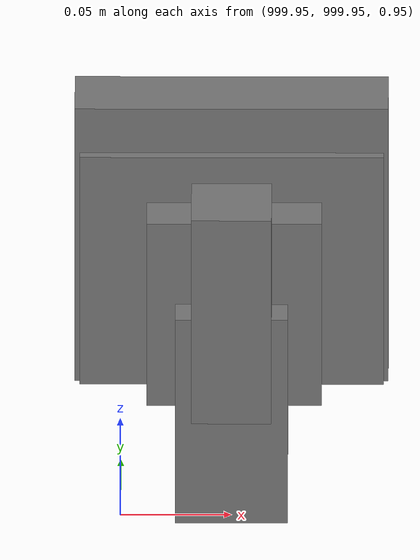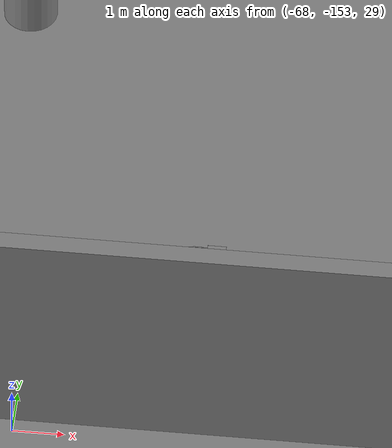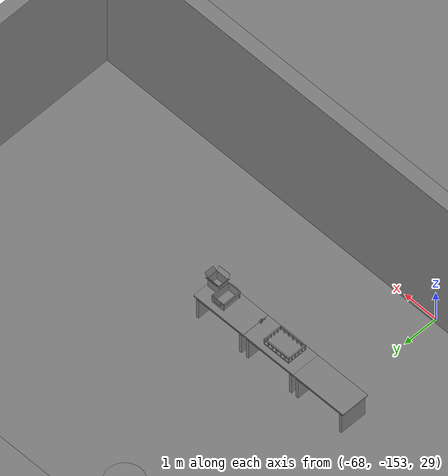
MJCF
<mujoco>
    <option gravity="0.000000000 0.000000000 -9.810000420" timestep="0.0049999999" integrator="implicitfast" density="1.225" viscosity="1.8000001e-05" noslip_iterations="10" iterations="100" sdf_iterations="50">
        <flag multiccd="disable"/>
    </option>
    <size memory="1000M"/>
    <compiler coordinate="local"/>
    <worldbody>
        <light cutoff="30" pos="0 1 1" dir="0 -1 -2"/>
        <light cutoff="30" pos="0 -1 1" dir="0 1 -2"/>
        <body pos="-64.866622925 -149.383972168 30.183746338" euler="89.999984741 89.999946594 0.000000000" name="openloong_gripper_2f85_fix_base_usda_bluebox_01">
            <geom contype="1" conaffinity="1" density="1000" type="box" material="" rgba="0.500000000 0.500000000 0.500000000 1.000000000" solimp="0.899999976 0.949999988 0.001000000" friction="1.000000000 0.005000000 0.000100000" solref="0.020000000 1.000000000" margin="0" condim="3" group="0" pos="0.276580811 0.187225342 0.000068665" quat="0.707106948 0.000077471 0.707106352 0.000077486" size="0.100000001 0.057999998 0.010000000" name="openloong_gripper_2f85_fix_base_usda_geom_77F552DB_65CA_41BB_950E_90786199EC7B"/>
            <geom contype="1" conaffinity="1" density="1000" type="box" material="" rgba="0.500000000 0.500000000 0.500000000 1.000000000" solimp="0.899999976 0.949999988 0.001000000" friction="1.000000000 0.005000000 0.000100000" solref="0.020000000 1.000000000" margin="0" condim="3" group="0" pos="0.000000000 0.002883911 0.000000000" quat="0.999999881 0.000000000 0.000000000 0.000000000" size="0.254000008 0.003000000 0.172000006" name="openloong_gripper_2f85_fix_base_usda_geom_D1F647F7_E561_45A1_9C19_DECFFCE7174B"/>
            <geom contype="1" conaffinity="1" density="1000" type="box" material="" rgba="0.500000000 0.500000000 0.500000000 1.000000000" solimp="0.899999976 0.949999988 0.001000000" friction="1.000000000 0.005000000 0.000100000" solref="0.020000000 1.000000000" margin="0" condim="3" group="0" pos="0.000000000 0.124874115 0.173484802" quat="0.999796331 0.020176515 -0.000000015 0.000000030" size="0.259999990 0.119999997 0.007000000" name="openloong_gripper_2f85_fix_base_usda_geom_E937B5E0_EF4C_465A_9D48_98B2F656AEB5"/>
            <geom contype="1" conaffinity="1" density="1000" type="box" material="" rgba="0.500000000 0.500000000 0.500000000 1.000000000" solimp="0.899999976 0.949999988 0.001000000" friction="1.000000000 0.005000000 0.000100000" solref="0.020000000 1.000000000" margin="0" condim="3" group="0" pos="0.000000000 0.124874115 -0.173469543" quat="0.999796331 -0.020176545 -0.000000015 0.000000000" size="0.259999990 0.119999997 0.007000000" name="openloong_gripper_2f85_fix_base_usda_geom_5D12F4C5_971E_4C41_AEF4_6DA96A7D4B9F"/>
            <geom contype="1" conaffinity="1" density="1000" type="box" material="" rgba="0.500000000 0.500000000 0.500000000 1.000000000" solimp="0.899999976 0.949999988 0.001000000" friction="1.000000000 0.005000000 0.000100000" solref="0.020000000 1.000000000" margin="0" condim="3" group="0" pos="0.000000000 0.214008331 0.188980103" quat="0.999912977 0.013176724 0.000000015 0.000000000" size="0.259999990 0.029999999 0.012500000" name="openloong_gripper_2f85_fix_base_usda_geom_4973A312_A613_40EE_9C0E_71C8EA955760"/>
            <geom contype="1" conaffinity="1" density="1000" type="box" material="" rgba="0.500000000 0.500000000 0.500000000 1.000000000" solimp="0.899999976 0.949999988 0.001000000" friction="1.000000000 0.005000000 0.000100000" solref="0.020000000 1.000000000" margin="0" condim="3" group="0" pos="-0.258361816 0.125289917 0.001876831" quat="0.702796936 -0.020792112 0.710783124 0.020769298" size="0.189999998 0.119999997 0.009000000" name="openloong_gripper_2f85_fix_base_usda_geom_0E3FC716_587A_4544_A5BA_F34729F97B50"/>
            <geom contype="1" conaffinity="1" density="1000" type="box" material="" rgba="0.500000000 0.500000000 0.500000000 1.000000000" solimp="0.899999976 0.949999988 0.001000000" friction="1.000000000 0.005000000 0.000100000" solref="0.020000000 1.000000000" margin="0" condim="3" group="0" pos="0.000000000 0.214008331 -0.188980103" quat="0.999912977 -0.013176769 0.000000030 0.000000015" size="0.259999990 0.029999999 0.012500000" name="openloong_gripper_2f85_fix_base_usda_geom_773AFD16_58E3_44FA_93D2_CAE0868C7CA9"/>
            <geom contype="1" conaffinity="1" density="1000" type="box" material="" rgba="0.500000000 0.500000000 0.500000000 1.000000000" solimp="0.899999976 0.949999988 0.001000000" friction="1.000000000 0.005000000 0.000100000" solref="0.020000000 1.000000000" margin="0" condim="3" group="0" pos="-0.276611328 0.187225342 0.000068665" quat="0.707106650 0.000077441 0.707106709 0.000077456" size="0.100000001 0.057999998 0.010000000" name="openloong_gripper_2f85_fix_base_usda_geom_1AABDF3C_5073_49AD_9378_7869FB3FE06B"/>
            <geom contype="1" conaffinity="1" density="1000" type="box" material="" rgba="0.500000000 0.500000000 0.500000000 1.000000000" solimp="0.899999976 0.949999988 0.001000000" friction="1.000000000 0.005000000 0.000100000" solref="0.020000000 1.000000000" margin="0" condim="3" group="0" pos="0.258331299 0.125289917 0.001876831" quat="0.702851415 0.018856421 0.710823774 -0.019329369" size="0.189999998 0.119999997 0.009000000" name="openloong_gripper_2f85_fix_base_usda_geom_629D495C_6E67_4A84_84A3_3FED1BF6794E"/>
            <freejoint name="openloong_gripper_2f85_fix_base_usda_bluebox_01_joint"/>
            <site size="0.005000000 0.005000000 0.005000000" rgba="0.500000000 0.500000000 0.500000000 1.000000000" pos="0.000000000 0.000000000 0.000000000" quat="0.999961913 0.008726534 0.000000000 0.000000000" group="0" type="sphere" name="openloong_gripper_2f85_fix_base_usda_bluebox_01site"/>
        </body>
        <body pos="-64.496299744 -149.491867065 30.235729218" euler="0.000000000 0.000000000 89.999946594" name="openloong_gripper_2f85_fix_base_usda_cardboardbox_01">
            <geom contype="1" conaffinity="1" density="1000" type="box" material="" rgba="0.500000000 0.500000000 0.500000000 1.000000000" solimp="0.899999976 0.949999988 0.001000000" friction="1.000000000 0.005000000 0.000100000" solref="0.020000000 1.000000000" margin="0" condim="3" group="0" pos="-0.003166199 -0.004086494 0.005052090" quat="1.000000000 0.000000000 0.000000000 0.000000000" size="0.142499998 0.177500010 0.005000000" name="openloong_gripper_2f85_fix_base_usda_geom_3C5BD38F_2FC4_4899_80A3_71623B6C010C"/>
            <geom contype="1" conaffinity="1" density="1000" type="box" material="" rgba="0.500000000 0.500000000 0.500000000 1.000000000" solimp="0.899999976 0.949999988 0.001000000" friction="1.000000000 0.005000000 0.000100000" solref="0.020000000 1.000000000" margin="0" condim="3" group="0" pos="-0.003166199 0.170316696 0.150570869" quat="1.000000000 0.000000000 0.000000000 0.000000000" size="0.142499998 0.005000000 0.149999991" name="openloong_gripper_2f85_fix_base_usda_geom_828FCD47_9D70_40A9_9F48_40A06FFFB923"/>
            <geom contype="1" conaffinity="1" density="1000" type="box" material="" rgba="0.500000000 0.500000000 0.500000000 1.000000000" solimp="0.899999976 0.949999988 0.001000000" friction="1.000000000 0.005000000 0.000100000" solref="0.020000000 1.000000000" margin="0" condim="3" group="0" pos="-0.147399902 -0.005307198 0.150570869" quat="1.000000000 0.000000000 0.000000000 0.000000000" size="0.005000000 0.177500010 0.149999991" name="openloong_gripper_2f85_fix_base_usda_geom_1169DEE8_D1A2_486C_B4DF_EE511BF0230C"/>
            <geom contype="1" conaffinity="1" density="1000" type="box" material="" rgba="0.500000000 0.500000000 0.500000000 1.000000000" solimp="0.899999976 0.949999988 0.001000000" friction="1.000000000 0.005000000 0.000100000" solref="0.020000000 1.000000000" margin="0" condim="3" group="0" pos="0.140275955 -0.005307198 0.150570869" quat="1.000000000 0.000000000 0.000000000 0.000000000" size="0.005000000 0.177500010 0.149999991" name="openloong_gripper_2f85_fix_base_usda_geom_193E46EE_3BE5_4ED0_9162_7D266A5EA057"/>
            <geom contype="1" conaffinity="1" density="1000" type="box" material="" rgba="0.500000000 0.500000000 0.500000000 1.000000000" solimp="0.899999976 0.949999988 0.001000000" friction="1.000000000 0.005000000 0.000100000" solref="0.020000000 1.000000000" margin="0" condim="3" group="0" pos="-0.003166199 -0.181550980 0.150570869" quat="1.000000000 0.000000000 0.000000000 0.000000000" size="0.142499998 0.005000000 0.149999991" name="openloong_gripper_2f85_fix_base_usda_geom_0236CA3A_BBE1_42D3_88C3_555385F031B1"/>
            <freejoint name="openloong_gripper_2f85_fix_base_usda_cardboardbox_01_joint"/>
            <site size="0.005000000 0.005000000 0.005000000" rgba="0.500000000 0.500000000 0.500000000 1.000000000" pos="0.000000000 0.000000000 0.000000000" quat="0.999961913 0.008726535 0.000000000 0.000000000" group="0" type="sphere" name="openloong_gripper_2f85_fix_base_usda_site_434B8B6A_99B9_4B8C_8172_A8FB5AFC1E81"/>
            <body pos="0.139160156 -0.004048347 0.301930904" euler="-179.999954224 49.383502960 179.999954224" name="openloong_gripper_2f85_fix_base_usda_A1_006">
                <geom contype="1" conaffinity="1" density="1000" type="box" material="" rgba="0.500000000 0.500000000 0.500000000 1.000000000" solimp="0.899999976 0.949999988 0.001000000" friction="1.000000000 0.005000000 0.000100000" solref="0.020000000 1.000000000" margin="0" condim="3" group="0" pos="-0.071587563 0.000009537 0.001745224" quat="0.999999881 0.000000000 0.000000000 0.000000000" size="0.071249999 0.179999992 0.002500000" name="openloong_gripper_2f85_fix_base_usda_geom_AF416FCA_49C8_453F_8B59_9E5550BB0AF0"/>
                <joint armature="0" stiffness="0.07" damping="0.0099999998" axis="0.000000 1.000000 0.000000" type="hinge" name="openloong_gripper_2f85_fix_base_usda_A1_006"/>
            </body>
            <body pos="-0.145902634 -0.004086494 0.301938057" euler="-180.000000000 -60.000011444 -180.000000000" name="openloong_gripper_2f85_fix_base_usda_A2_006">
                <geom contype="1" conaffinity="1" density="1000" type="box" material="" rgba="0.500000000 0.500000000 0.500000000 1.000000000" solimp="0.899999976 0.949999988 0.001000000" friction="1.000000000 0.005000000 0.000100000" solref="0.020000000 1.000000000" margin="0" condim="3" group="0" pos="0.071268082 0.000009537 0.002717972" quat="0.000002921 0.000000000 -0.000000030 0.999999881" size="0.071249999 0.179999992 0.002500000" name="openloong_gripper_2f85_fix_base_usda_geom_896773BA_F1D6_497D_8052_0AE2EF869CC8"/>
                <joint armature="0" stiffness="0.07" damping="0.0099999998" axis="0.000000 1.000000 0.000000" type="hinge" name="openloong_gripper_2f85_fix_base_usda_A2_006"/>
            </body>
            <body pos="-0.003385544 0.175991058 0.301930904" euler="-125.858116150 -0.000004561 0.000002331" name="openloong_gripper_2f85_fix_base_usda_B2_006">
                <geom contype="1" conaffinity="1" density="1000" type="box" material="" rgba="0.500000000 0.500000000 0.500000000 1.000000000" solimp="0.899999976 0.949999988 0.001000000" friction="1.000000000 0.005000000 0.000100000" solref="0.020000000 1.000000000" margin="0" condim="3" group="0" pos="0.000009537 -0.070939064 -0.002470016" quat="0.999614120 0.027776197 -0.000000015 0.000000030" size="0.137500003 0.064999998 0.005000000" name="openloong_gripper_2f85_fix_base_usda_geom_FBC40AF0_8A07_4064_98E9_DC52A227C027"/>
                <joint armature="0" stiffness="0.07" damping="0.0099999998" axis="1.000000 0.000000 0.000000" type="hinge" name="openloong_gripper_2f85_fix_base_usda_B2_006"/>
            </body>
            <body pos="-0.003385544 -0.184140205 0.301938057" euler="147.805557251 0.000000000 0.000000000" name="openloong_gripper_2f85_fix_base_usda_B1_006">
                <geom contype="1" conaffinity="1" density="1000" type="box" material="" rgba="0.500000000 0.500000000 0.500000000 1.000000000" solimp="0.899999976 0.949999988 0.001000000" friction="1.000000000 0.005000000 0.000100000" solref="0.020000000 1.000000000" margin="0" condim="3" group="0" pos="-0.000028610 0.070202351 -0.002703667" quat="0.999614179 -0.027776167 0.000000000 0.000000000" size="0.137500003 0.064999998 0.005000000" name="openloong_gripper_2f85_fix_base_usda_geom_C57B8FE2_C80A_409A_B671_8B23356D364D"/>
                <joint armature="0" stiffness="0.07" damping="0.0099999998" axis="1.000000 0.000000 0.000000" type="hinge" name="openloong_gripper_2f85_fix_base_usda_B1_006"/>
            </body>
        </body>
        <body pos="-65.882858276 -149.481979370 30.229999542" euler="-64.487716675 0.000000000 0.000000000" name="openloong_gripper_2f85_fix_base_usda_Barcode">
            <geom contype="1" conaffinity="1" density="1000" type="box" material="" rgba="0.500000000 0.500000000 0.500000000 1.000000000" solimp="0.899999976 0.949999988 0.001000000" friction="1.000000000 0.005000000 0.000100000" solref="0.020000000 1.000000000" margin="0" condim="3" group="0" pos="0.000000000 0.013038635 0.001419067" quat="0.000000000 0.000000000 0.000000000 1.000000119" size="0.034000002 0.010000000 0.017999999" name="openloong_gripper_2f85_fix_base_usda_geom_FA6C4C41_FADD_47AE_B17C_9B988831F8B3"/>
            <geom contype="1" conaffinity="1" density="1000" type="box" material="" rgba="0.500000000 0.500000000 0.500000000 1.000000000" solimp="0.899999976 0.949999988 0.001000000" friction="1.000000000 0.005000000 0.000100000" solref="0.020000000 1.000000000" margin="0" condim="3" group="0" pos="0.000000000 -0.035301208 -0.007095337" quat="0.000000000 0.000000000 -0.043619365 0.999048233" size="0.028999999 0.010000000 0.020000000" name="openloong_gripper_2f85_fix_base_usda_geom_0895A36A_259E_474A_B08B_788928F2C1BE"/>
            <geom contype="1" conaffinity="1" density="1000" type="box" material="" rgba="0.500000000 0.500000000 0.500000000 1.000000000" solimp="0.899999976 0.949999988 0.001000000" friction="1.000000000 0.005000000 0.000100000" solref="0.020000000 1.000000000" margin="0" condim="3" group="0" pos="0.000000000 -0.043411255 -0.011749268" quat="0.922262907 0.386563420 0.000000000 0.000000000" size="0.026000001 0.010000000 0.020000000" name="openloong_gripper_2f85_fix_base_usda_geom_21556DCD_CDDB_482A_898C_8876E791CED4"/>
            <geom contype="1" conaffinity="1" density="1000" type="box" material="" rgba="0.500000000 0.500000000 0.500000000 1.000000000" solimp="0.899999976 0.949999988 0.001000000" friction="1.000000000 0.005000000 0.000100000" solref="0.020000000 1.000000000" margin="0" condim="3" group="0" pos="0.000000000 -0.016967773 -0.031860352" quat="0.000000000 0.000000000 0.000000000 1.000000119" size="0.008000000 0.010000000 0.013000000" name="openloong_gripper_2f85_fix_base_usda_geom_D2E68EDF_EC86_4D58_A919_F2FF6DA0342C"/>
            <geom contype="1" conaffinity="1" density="1000" type="box" material="" rgba="0.500000000 0.500000000 0.500000000 1.000000000" solimp="0.899999976 0.949999988 0.001000000" friction="1.000000000 0.005000000 0.000100000" solref="0.020000000 1.000000000" margin="0" condim="3" group="0" pos="0.000000000 -0.001869202 0.000312805" quat="0.953716993 0.300705761 0.000000000 0.000000000" size="0.032000002 0.010000000 0.018999999" name="openloong_gripper_2f85_fix_base_usda_geom_5587E1AA_6D87_42B1_8CFA_34DC812AECA9"/>
            <geom contype="1" conaffinity="1" density="1000" type="box" material="" rgba="0.500000000 0.500000000 0.500000000 1.000000000" solimp="0.899999976 0.949999988 0.001000000" friction="1.000000000 0.005000000 0.000100000" solref="0.020000000 1.000000000" margin="0" condim="3" group="0" pos="0.000000000 -0.019531250 -0.003173828" quat="0.953716993 0.300705761 0.000000000 0.000000000" size="0.030999999 0.010000000 0.020000000" name="openloong_gripper_2f85_fix_base_usda_geom_547DF0E3_A6D6_4408_896B_726356D1B97B"/>
            <geom contype="1" conaffinity="1" density="1000" type="box" material="" rgba="0.500000000 0.500000000 0.500000000 1.000000000" solimp="0.899999976 0.949999988 0.001000000" friction="1.000000000 0.005000000 0.000100000" solref="0.020000000 1.000000000" margin="0" condim="3" group="0" pos="0.000000000 -0.035301208 -0.007095337" quat="0.953716993 0.300705761 0.000000000 0.000000000" size="0.028999999 0.010000000 0.020000000" name="openloong_gripper_2f85_fix_base_usda_geom_452A1C5C_966A_4102_AE28_E80AE0E3FEAB"/>
            <geom contype="1" conaffinity="1" density="1000" type="box" material="" rgba="0.500000000 0.500000000 0.500000000 1.000000000" solimp="0.899999976 0.949999988 0.001000000" friction="1.000000000 0.005000000 0.000100000" solref="0.020000000 1.000000000" margin="0" condim="3" group="0" pos="0.000000000 -0.042617798 -0.071121216" quat="0.000000000 0.000000000 0.000000000 1.000000119" size="0.013000000 0.021000000 0.059999999" name="openloong_gripper_2f85_fix_base_usda_geom_7E36EDFA_022D_4A87_82D3_46E48EBF6397"/>
            <freejoint name="openloong_gripper_2f85_fix_base_usda_Barcode_joint"/>
            <site size="0.005000000 0.005000000 0.005000000" rgba="0.500000000 0.500000000 0.500000000 1.000000000" pos="0.000000000 0.000000000 0.000000000" quat="1.000000000 0.000000000 0.000000000 0.000000000" group="0" type="sphere" name="openloong_gripper_2f85_fix_base_usda_Barcode_site"/>
        </body>
        <body pos="-66.745018005 -149.392349243 30.184000015" euler="0.000000000 0.000000000 89.999946594" name="[22329767319778]_Basket_01">
            <geom contype="1" conaffinity="1" density="1000" type="box" material="" rgba="0.500000000 0.500000000 0.500000000 1.000000000" solimp="0.899999976 0.949999988 0.001000000" friction="1.000000000 0.005000000 0.000100000" solref="0.020000000 1.000000000" margin="0" condim="3" group="0" pos="-0.052425385 0.389207840 0.089787483" quat="0.707107008 0.000000000 0.000000000 0.707106411" size="0.014249999 0.014249999 0.059999999" name="[22329767319778]_geom_CFD4817D_A799_483F_928B_93553E82A010"/>
            <geom contype="1" conaffinity="1" density="1000" type="box" material="" rgba="0.500000000 0.500000000 0.500000000 1.000000000" solimp="0.899999976 0.949999988 0.001000000" friction="1.000000000 0.005000000 0.000100000" solref="0.020000000 1.000000000" margin="0" condim="3" group="0" pos="0.264015198 -0.133043289 0.089787483" quat="0.707107008 0.000000000 0.000000000 0.707106411" size="0.014249999 0.014249999 0.059999999" name="[22329767319778]_geom_8380D85A_FA8D_419E_B52E_3EBFCE3FED54"/>
            <geom contype="1" conaffinity="1" density="1000" type="box" material="" rgba="0.500000000 0.500000000 0.500000000 1.000000000" solimp="0.899999976 0.949999988 0.001000000" friction="1.000000000 0.005000000 0.000100000" solref="0.020000000 1.000000000" margin="0" condim="3" group="0" pos="-0.264015198 -0.265548706 0.089793205" quat="0.707107008 0.000000000 0.000000000 0.707106411" size="0.014249999 0.014249999 0.059999999" name="[22329767319778]_geom_4AD69205_E739_4732_A385_6A82667812E5"/>
            <geom contype="1" conaffinity="1" density="1000" type="box" material="" rgba="0.500000000 0.500000000 0.500000000 1.000000000" solimp="0.899999976 0.949999988 0.001000000" friction="1.000000000 0.005000000 0.000100000" solref="0.020000000 1.000000000" margin="0" condim="3" group="0" pos="-0.160263062 -0.389322281 0.089793205" quat="0.707107008 0.000000000 0.000000000 0.707106411" size="0.014249999 0.014249999 0.059999999" name="[22329767319778]_geom_28440093_22D4_44A6_8361_20EC941639F7"/>
            <geom contype="1" conaffinity="1" density="1000" type="box" material="" rgba="0.500000000 0.500000000 0.500000000 1.000000000" solimp="0.899999976 0.949999988 0.001000000" friction="1.000000000 0.005000000 0.000100000" solref="0.020000000 1.000000000" margin="0" condim="3" group="0" pos="0.162265778 -0.389322281 0.089787483" quat="0.707107008 0.000000000 0.000000000 0.707106411" size="0.014249999 0.014249999 0.059999999" name="[22329767319778]_geom_4A7157E2_C5AF_45C4_9657_93BF7422707A"/>
            <geom contype="1" conaffinity="1" density="1000" type="box" material="" rgba="0.500000000 0.500000000 0.500000000 1.000000000" solimp="0.899999976 0.949999988 0.001000000" friction="1.000000000 0.005000000 0.000100000" solref="0.020000000 1.000000000" margin="0" condim="3" group="0" pos="0.264015198 0.389207840 0.089787483" quat="0.707107008 0.000000000 0.000000000 0.707106411" size="0.014249999 0.014249999 0.059999999" name="[22329767319778]_geom_F970577E_14FE_45B9_9463_E107F574328F"/>
            <geom contype="1" conaffinity="1" density="1000" type="box" material="" rgba="0.500000000 0.500000000 0.500000000 1.000000000" solimp="0.899999976 0.949999988 0.001000000" friction="1.000000000 0.005000000 0.000100000" solref="0.020000000 1.000000000" margin="0" condim="3" group="0" pos="-0.264015198 -0.133043289 0.089793205" quat="0.707107008 0.000000000 0.000000000 0.707106411" size="0.014249999 0.014249999 0.059999999" name="[22329767319778]_geom_A912BF41_C821_403B_935F_7581172C4F41"/>
            <geom contype="1" conaffinity="1" density="1000" type="box" material="" rgba="0.500000000 0.500000000 0.500000000 1.000000000" solimp="0.899999976 0.949999988 0.001000000" friction="1.000000000 0.005000000 0.000100000" solref="0.020000000 1.000000000" margin="0" condim="3" group="0" pos="-0.264026642 0.269256592 0.089793205" quat="0.707107008 0.000000000 0.000000000 0.707106411" size="0.014249999 0.014249999 0.059999999" name="[22329767319778]_geom_E232BCE3_8906_49CA_9C7F_2B2760DC5267"/>
            <geom contype="1" conaffinity="1" density="1000" type="box" material="" rgba="0.500000000 0.500000000 0.500000000 1.000000000" solimp="0.899999976 0.949999988 0.001000000" friction="1.000000000 0.005000000 0.000100000" solref="0.020000000 1.000000000" margin="0" condim="3" group="0" pos="0.054462433 0.389207840 0.089787483" quat="0.707107008 0.000000000 0.000000000 0.707106411" size="0.014249999 0.014249999 0.059999999" name="[22329767319778]_geom_784A2BCE_72CF_4196_8336_D3643F47183A"/>
            <geom contype="1" conaffinity="1" density="1000" type="box" material="" rgba="0.500000000 0.500000000 0.500000000 1.000000000" solimp="0.899999976 0.949999988 0.001000000" friction="1.000000000 0.005000000 0.000100000" solref="0.020000000 1.000000000" margin="0" condim="3" group="0" pos="0.054462433 -0.389322281 0.089787483" quat="0.707107008 0.000000000 0.000000000 0.707106411" size="0.014249999 0.014249999 0.059999999" name="[22329767319778]_geom_C78B6C74_3CAC_4817_A26D_7AD83297CD5D"/>
            <geom contype="1" conaffinity="1" density="1000" type="box" material="" rgba="0.500000000 0.500000000 0.500000000 1.000000000" solimp="0.899999976 0.949999988 0.001000000" friction="1.000000000 0.005000000 0.000100000" solref="0.020000000 1.000000000" margin="0" condim="3" group="0" pos="0.264015198 0.269256592 0.089793205" quat="0.707107008 0.000000000 0.000000000 0.707106411" size="0.014249999 0.014249999 0.059999999" name="[22329767319778]_geom_E6376A46_7606_40DF_9DAD_C709EF081870"/>
            <geom contype="1" conaffinity="1" density="1000" type="box" material="" rgba="0.500000000 0.500000000 0.500000000 1.000000000" solimp="0.899999976 0.949999988 0.001000000" friction="1.000000000 0.005000000 0.000100000" solref="0.020000000 1.000000000" margin="0" condim="3" group="0" pos="0.264015198 -0.389322281 0.089787483" quat="0.707107008 0.000000000 0.000000000 0.707106411" size="0.014249999 0.014249999 0.059999999" name="[22329767319778]_geom_5981BF50_685F_404A_A2EC_926912E390BB"/>
            <geom contype="1" conaffinity="1" density="1000" type="box" material="" rgba="0.500000000 0.500000000 0.500000000 1.000000000" solimp="0.899999976 0.949999988 0.001000000" friction="1.000000000 0.005000000 0.000100000" solref="0.020000000 1.000000000" margin="0" condim="3" group="0" pos="0.000000000 0.000000000 0.015998840" quat="0.707107008 0.000000000 0.000000000 0.707106411" size="0.403499991 0.279000014 0.015750000" name="[22329767319778]_geom_B048222C_0D66_441B_AF61_76B3D41279AB"/>
            <geom contype="1" conaffinity="1" density="1000" type="box" material="" rgba="0.500000000 0.500000000 0.500000000 1.000000000" solimp="0.899999976 0.949999988 0.001000000" friction="1.000000000 0.005000000 0.000100000" solref="0.020000000 1.000000000" margin="0" condim="3" group="0" pos="0.000000000 -0.389476776 0.163619041" quat="0.707107008 0.000000000 0.000000000 0.707106411" size="0.015000000 0.277500004 0.015750000" name="[22329767319778]_geom_7A7E6221_BC68_4210_A5C6_BB99007C008D"/>
            <geom contype="1" conaffinity="1" density="1000" type="box" material="" rgba="0.500000000 0.500000000 0.500000000 1.000000000" solimp="0.899999976 0.949999988 0.001000000" friction="1.000000000 0.005000000 0.000100000" solref="0.020000000 1.000000000" margin="0" condim="3" group="0" pos="0.162265778 0.389207840 0.089787483" quat="0.707107008 0.000000000 0.000000000 0.707106411" size="0.014249999 0.014249999 0.059999999" name="[22329767319778]_geom_4FBDC521_C244_41FE_97D7_DA2CE86CF4CE"/>
            <geom contype="1" conaffinity="1" density="1000" type="box" material="" rgba="0.500000000 0.500000000 0.500000000 1.000000000" solimp="0.899999976 0.949999988 0.001000000" friction="1.000000000 0.005000000 0.000100000" solref="0.020000000 1.000000000" margin="0" condim="3" group="0" pos="0.000000000 0.389471054 0.163619041" quat="0.707107008 0.000000000 0.000000000 0.707106411" size="0.015000000 0.277500004 0.015750000" name="[22329767319778]_geom_932F61F1_CD78_48F0_874A_93F7E539AA51"/>
            <geom contype="1" conaffinity="1" density="1000" type="box" material="" rgba="0.500000000 0.500000000 0.500000000 1.000000000" solimp="0.899999976 0.949999988 0.001000000" friction="1.000000000 0.005000000 0.000100000" solref="0.020000000 1.000000000" margin="0" condim="3" group="0" pos="-0.263511658 0.000000000 0.163619041" quat="0.707107008 0.000000000 0.000000000 0.707106411" size="0.403499991 0.015000000 0.015750000" name="[22329767319778]_geom_726229FA_0DF3_4396_A8E5_2CBC3A457389"/>
            <geom contype="1" conaffinity="1" density="1000" type="box" material="" rgba="0.500000000 0.500000000 0.500000000 1.000000000" solimp="0.899999976 0.949999988 0.001000000" friction="1.000000000 0.005000000 0.000100000" solref="0.020000000 1.000000000" margin="0" condim="3" group="0" pos="-0.264015198 0.141334534 0.089793205" quat="0.707107008 0.000000000 0.000000000 0.707106411" size="0.014249999 0.014249999 0.059999999" name="[22329767319778]_geom_85784838_F05A_4C2C_B618_A9824206EC97"/>
            <geom contype="1" conaffinity="1" density="1000" type="box" material="" rgba="0.500000000 0.500000000 0.500000000 1.000000000" solimp="0.899999976 0.949999988 0.001000000" friction="1.000000000 0.005000000 0.000100000" solref="0.020000000 1.000000000" margin="0" condim="3" group="0" pos="0.264015198 -0.265548706 0.089787483" quat="0.707107008 0.000000000 0.000000000 0.707106411" size="0.014249999 0.014249999 0.059999999" name="[22329767319778]_geom_4CA038B0_2306_4B9D_8376_EBD0852B38C7"/>
            <geom contype="1" conaffinity="1" density="1000" type="box" material="" rgba="0.500000000 0.500000000 0.500000000 1.000000000" solimp="0.899999976 0.949999988 0.001000000" friction="1.000000000 0.005000000 0.000100000" solref="0.020000000 1.000000000" margin="0" condim="3" group="0" pos="-0.160263062 0.389207840 0.089787483" quat="0.707107008 0.000000000 0.000000000 0.707106411" size="0.014249999 0.014249999 0.059999999" name="[22329767319778]_geom_FF51E37F_FD97_40CD_9EDB_337B32E22839"/>
            <geom contype="1" conaffinity="1" density="1000" type="box" material="" rgba="0.500000000 0.500000000 0.500000000 1.000000000" solimp="0.899999976 0.949999988 0.001000000" friction="1.000000000 0.005000000 0.000100000" solref="0.020000000 1.000000000" margin="0" condim="3" group="0" pos="-0.052425385 -0.389322281 0.089787483" quat="0.707107008 0.000000000 0.000000000 0.707106411" size="0.014249999 0.014249999 0.059999999" name="[22329767319778]_geom_2E656731_EA01_4550_8DF7_B262E409B9B6"/>
            <geom contype="1" conaffinity="1" density="1000" type="box" material="" rgba="0.500000000 0.500000000 0.500000000 1.000000000" solimp="0.899999976 0.949999988 0.001000000" friction="1.000000000 0.005000000 0.000100000" solref="0.020000000 1.000000000" margin="0" condim="3" group="0" pos="-0.264026642 -0.389322281 0.089793205" quat="0.707107008 0.000000000 0.000000000 0.707106411" size="0.014249999 0.014249999 0.059999999" name="[22329767319778]_geom_4FA55BF0_E035_4396_962A_0CA620502444"/>
            <geom contype="1" conaffinity="1" density="1000" type="box" material="" rgba="0.500000000 0.500000000 0.500000000 1.000000000" solimp="0.899999976 0.949999988 0.001000000" friction="1.000000000 0.005000000 0.000100000" solref="0.020000000 1.000000000" margin="0" condim="3" group="0" pos="0.264015198 0.141334534 0.089787483" quat="0.707107008 0.000000000 0.000000000 0.707106411" size="0.014249999 0.014249999 0.059999999" name="[22329767319778]_geom_EC91DA35_4948_4EF4_92B7_B8FD1D678B46"/>
            <geom contype="1" conaffinity="1" density="1000" type="box" material="" rgba="0.500000000 0.500000000 0.500000000 1.000000000" solimp="0.899999976 0.949999988 0.001000000" friction="1.000000000 0.005000000 0.000100000" solref="0.020000000 1.000000000" margin="0" condim="3" group="0" pos="-0.264015198 0.389207840 0.089793205" quat="0.707107008 0.000000000 0.000000000 0.707106411" size="0.014249999 0.014249999 0.059999999" name="[22329767319778]_geom_E050E35B_6DB1_4529_8DB8_3878002C5C06"/>
            <geom contype="1" conaffinity="1" density="1000" type="box" material="" rgba="0.500000000 0.500000000 0.500000000 1.000000000" solimp="0.899999976 0.949999988 0.001000000" friction="1.000000000 0.005000000 0.000100000" solref="0.020000000 1.000000000" margin="0" condim="3" group="0" pos="0.264015198 0.004480362 0.089787483" quat="0.707107008 0.000000000 0.000000000 0.707106411" size="0.014249999 0.014249999 0.059999999" name="[22329767319778]_geom_BF2441C0_D986_449E_A31B_0F5098D736A3"/>
            <geom contype="1" conaffinity="1" density="1000" type="box" material="" rgba="0.500000000 0.500000000 0.500000000 1.000000000" solimp="0.899999976 0.949999988 0.001000000" friction="1.000000000 0.005000000 0.000100000" solref="0.020000000 1.000000000" margin="0" condim="3" group="0" pos="0.263694763 -0.000011444 0.163619041" quat="0.707107008 0.000000000 0.000000000 0.707106411" size="0.403499991 0.015000000 0.015750000" name="[22329767319778]_geom_1331DEA5_86FB_4813_A833_F18E62127943"/>
            <geom contype="1" conaffinity="1" density="1000" type="box" material="" rgba="0.500000000 0.500000000 0.500000000 1.000000000" solimp="0.899999976 0.949999988 0.001000000" friction="1.000000000 0.005000000 0.000100000" solref="0.020000000 1.000000000" margin="0" condim="3" group="0" pos="-0.264015198 0.004480362 0.089793205" quat="0.707107008 0.000000000 0.000000000 0.707106411" size="0.014249999 0.014249999 0.059999999" name="[22329767319778]_geom_1A51C2F9_5F5E_486C_BFF0_D8CDC190F772"/>
            <freejoint name="[22329767319778]_joint_80399FB8_7B61_42BE_AD40_3C6D237C6833"/>
        </body>
        <body pos="0.000000000 0.000000000 0.000000000" euler="0.000000000 0.000000000 0.000000000" name="Static Objects_Static Objects">
            <geom contype="1" conaffinity="1" density="1000" type="box" material="" rgba="0.500000000 0.500000000 0.500000000 1.000000000" solimp="0.899999976 0.949999988 0.001000000" friction="1.000000000 0.005000000 0.000100000" solref="0.020000000 1.000000000" margin="0" condim="3" group="0" pos="-67.544113159 -149.365814209 29.727830887" quat="0.500000417 0.499999970 0.499999553 0.499999970" size="0.381000012 0.319999993 0.041000001" name="Static Objects_geom_568C953D_6AEB_4422_AF02_97CCD286383E"/>
            <geom contype="1" conaffinity="1" density="1000" type="box" material="" rgba="0.500000000 0.500000000 0.500000000 1.000000000" solimp="0.899999976 0.949999988 0.001000000" friction="1.000000000 0.005000000 0.000100000" solref="0.020000000 1.000000000" margin="0" condim="3" group="0" pos="-68.239501953 -149.365814209 30.086868286" quat="0.500000417 0.499999970 0.499999553 0.499999970" size="0.370999992 0.039500002 0.745000005" name="Static Objects_geom_E091D12A_02D9_4222_8CA6_FB141C3CE656"/>
            <geom contype="1" conaffinity="1" density="1000" type="box" material="" rgba="0.500000000 0.500000000 0.500000000 1.000000000" solimp="0.899999976 0.949999988 0.001000000" friction="1.000000000 0.005000000 0.000100000" solref="0.020000000 1.000000000" margin="0" condim="3" group="0" pos="-68.239501953 -149.365814209 30.147235870" quat="0.500000417 0.499999970 0.499999553 0.499999970" size="0.400000006 0.022000000 0.800000012" name="Static Objects_geom_87DB4168_43A1_4212_AE34_E3528FC97359"/>
            <geom contype="1" conaffinity="1" density="1000" type="box" material="" rgba="0.500000000 0.500000000 0.500000000 1.000000000" solimp="0.899999976 0.949999988 0.001000000" friction="1.000000000 0.005000000 0.000100000" solref="0.020000000 1.000000000" margin="0" condim="3" group="0" pos="-68.934890747 -149.365814209 29.727830887" quat="0.500000417 0.499999970 0.499999553 0.499999970" size="0.381000012 0.319999993 0.041000001" name="Static Objects_geom_660A4646_81FD_4FC3_9492_0BBAD611161A"/>
            <geom contype="1" conaffinity="1" density="1000" type="box" material="" rgba="0.500000000 0.500000000 0.500000000 1.000000000" solimp="0.899999976 0.949999988 0.001000000" friction="1.000000000 0.005000000 0.000100000" solref="0.020000000 1.000000000" margin="0" condim="3" group="0" pos="-68.239501953 -149.365814209 29.561563492" quat="0.500000417 0.499999970 0.499999553 0.499999970" size="0.020000000 0.022000000 0.660000026" name="Static Objects_geom_EF657E1B_CFDA_4AC6_9AAB_C4B3053A424B"/>
            <geom contype="1" conaffinity="1" density="1000" type="box" material="" rgba="0.500000000 0.500000000 0.500000000 1.000000000" solimp="0.899999976 0.949999988 0.001000000" friction="1.000000000 0.005000000 0.000100000" solref="0.020000000 1.000000000" margin="0" condim="3" group="0" pos="-65.945671082 -149.365814209 29.727830887" quat="0.500000417 0.499999970 0.499999553 0.499999970" size="0.381000012 0.319999993 0.041000001" name="Static Objects_geom_8D6052F8_359B_49D2_BCF7_10C6DEAAA9DB"/>
            <geom contype="1" conaffinity="1" density="1000" type="box" material="" rgba="0.500000000 0.500000000 0.500000000 1.000000000" solimp="0.899999976 0.949999988 0.001000000" friction="1.000000000 0.005000000 0.000100000" solref="0.020000000 1.000000000" margin="0" condim="3" group="0" pos="-66.641059875 -149.365814209 30.086868286" quat="0.500000417 0.499999970 0.499999553 0.499999970" size="0.370999992 0.039500002 0.745000005" name="Static Objects_geom_EF024F4C_061F_458D_BFA5_0231823DA6DE"/>
            <geom contype="1" conaffinity="1" density="1000" type="box" material="" rgba="0.500000000 0.500000000 0.500000000 1.000000000" solimp="0.899999976 0.949999988 0.001000000" friction="1.000000000 0.005000000 0.000100000" solref="0.020000000 1.000000000" margin="0" condim="3" group="0" pos="-66.641059875 -149.365814209 30.147235870" quat="0.500000417 0.499999970 0.499999553 0.499999970" size="0.400000006 0.022000000 0.800000012" name="Static Objects_geom_BB828178_FCFE_4558_8CDF_4D9EA5BE6F19"/>
            <geom contype="1" conaffinity="1" density="1000" type="box" material="" rgba="0.500000000 0.500000000 0.500000000 1.000000000" solimp="0.899999976 0.949999988 0.001000000" friction="1.000000000 0.005000000 0.000100000" solref="0.020000000 1.000000000" margin="0" condim="3" group="0" pos="-67.336448669 -149.365814209 29.727830887" quat="0.500000417 0.499999970 0.499999553 0.499999970" size="0.381000012 0.319999993 0.041000001" name="Static Objects_geom_65500B19_CF5D_48DA_9FE2_C3CF7DAA2BC6"/>
            <geom contype="1" conaffinity="1" density="1000" type="box" material="" rgba="0.500000000 0.500000000 0.500000000 1.000000000" solimp="0.899999976 0.949999988 0.001000000" friction="1.000000000 0.005000000 0.000100000" solref="0.020000000 1.000000000" margin="0" condim="3" group="0" pos="-66.641059875 -149.365814209 29.561563492" quat="0.500000417 0.499999970 0.499999553 0.499999970" size="0.020000000 0.022000000 0.660000026" name="Static Objects_geom_C8CA5A56_DAB8_47A2_BE96_1300DB62001C"/>
            <geom contype="1" conaffinity="1" density="1000" type="box" material="" rgba="0.500000000 0.500000000 0.500000000 1.000000000" solimp="0.899999976 0.949999988 0.001000000" friction="1.000000000 0.005000000 0.000100000" solref="0.020000000 1.000000000" margin="0" condim="3" group="0" pos="-64.338577271 -149.365814209 29.727830887" quat="0.500000417 0.499999970 0.499999553 0.499999970" size="0.381000012 0.319999993 0.041000001" name="Static Objects_geom_C8E7CCFC_F6A8_414F_B97C_C40B4FE90B72"/>
            <geom contype="1" conaffinity="1" density="1000" type="box" material="" rgba="0.500000000 0.500000000 0.500000000 1.000000000" solimp="0.899999976 0.949999988 0.001000000" friction="1.000000000 0.005000000 0.000100000" solref="0.020000000 1.000000000" margin="0" condim="3" group="0" pos="-65.033966064 -149.365814209 30.086868286" quat="0.500000417 0.499999970 0.499999553 0.499999970" size="0.370999992 0.039500002 0.745000005" name="Static Objects_geom_D7D91F1A_37E3_42FA_8DB9_8B9E6E8F0D4D"/>
            <geom contype="1" conaffinity="1" density="1000" type="box" material="" rgba="0.500000000 0.500000000 0.500000000 1.000000000" solimp="0.899999976 0.949999988 0.001000000" friction="1.000000000 0.005000000 0.000100000" solref="0.020000000 1.000000000" margin="0" condim="3" group="0" pos="-65.033966064 -149.365814209 30.147235870" quat="0.500000417 0.499999970 0.499999553 0.499999970" size="0.400000006 0.022000000 0.800000012" name="Static Objects_geom_66797682_3CDD_4CE2_94D9_125AAB001B7E"/>
            <geom contype="1" conaffinity="1" density="1000" type="box" material="" rgba="0.500000000 0.500000000 0.500000000 1.000000000" solimp="0.899999976 0.949999988 0.001000000" friction="1.000000000 0.005000000 0.000100000" solref="0.020000000 1.000000000" margin="0" condim="3" group="0" pos="-65.729354858 -149.365814209 29.727830887" quat="0.500000417 0.499999970 0.499999553 0.499999970" size="0.381000012 0.319999993 0.041000001" name="Static Objects_geom_F0BCEF14_A1B0_4A1C_B13E_3C3532BCCCA8"/>
            <geom contype="1" conaffinity="1" density="1000" type="box" material="" rgba="0.500000000 0.500000000 0.500000000 1.000000000" solimp="0.899999976 0.949999988 0.001000000" friction="1.000000000 0.005000000 0.000100000" solref="0.020000000 1.000000000" margin="0" condim="3" group="0" pos="-65.033966064 -149.365814209 29.561563492" quat="0.500000417 0.499999970 0.499999553 0.499999970" size="0.020000000 0.022000000 0.660000026" name="Static Objects_geom_D8152DCB_D47D_49F2_9825_112E1C690A54"/>
            <geom contype="1" conaffinity="1" density="1000" type="box" material="" rgba="0.500000000 0.500000000 0.500000000 1.000000000" solimp="0.899999976 0.949999988 0.001000000" friction="1.000000000 0.005000000 0.000100000" solref="0.020000000 1.000000000" margin="0" condim="3" group="0" pos="-61.754566193 -137.853729248 33.906845093" quat="0.707107067 0.000000000 0.000000000 0.707106471" size="0.759999990 0.759999990 4.500000000" name="Static Objects_geom_88D2EACC_A136_49BB_AF7C_0882FF9898B2"/>
            <geom contype="1" conaffinity="1" density="1000" type="box" material="" rgba="0.500000000 0.500000000 0.500000000 1.000000000" solimp="0.899999976 0.949999988 0.001000000" friction="1.000000000 0.005000000 0.000100000" solref="0.020000000 1.000000000" margin="0" condim="3" group="0" pos="-57.511135101 -144.927108765 31.707921982" quat="1.000000000 0.000000000 0.000000000 0.000000000" size="0.200000003 8.000000000 2.299999952" name="Static Objects_geom_61383F6A_B2B5_4F82_B6E8_67C7D530BD63"/>
            <geom contype="1" conaffinity="1" density="1000" type="box" material="" rgba="0.500000000 0.500000000 0.500000000 1.000000000" solimp="0.899999976 0.949999988 0.001000000" friction="1.000000000 0.005000000 0.000100000" solref="0.020000000 1.000000000" margin="0" condim="3" group="0" pos="-80.517646790 -157.574050903 31.688196182" quat="0.707107067 0.000000000 0.000000000 0.707106471" size="0.600000024 0.600000024 2.299999952" name="Static Objects_geom_F61ED761_E48F_4876_8068_451FDC569A71"/>
            <geom contype="1" conaffinity="1" density="1000" type="box" material="" rgba="0.500000000 0.500000000 0.500000000 1.000000000" solimp="0.899999976 0.949999988 0.001000000" friction="1.000000000 0.005000000 0.000100000" solref="0.020000000 1.000000000" margin="0" condim="3" group="0" pos="-80.711044312 -147.414932251 31.666158676" quat="1.000000000 0.000000000 0.000000000 0.000000000" size="0.200000003 10.000000000 2.299999952" name="Static Objects_geom_E5F67326_9142_4C65_ACFB_B4354315A949"/>
            <geom contype="1" conaffinity="1" density="1000" type="box" material="" rgba="0.500000000 0.500000000 0.500000000 1.000000000" solimp="0.899999976 0.949999988 0.001000000" friction="1.000000000 0.005000000 0.000100000" solref="0.020000000 1.000000000" margin="0" condim="3" group="0" pos="-57.687217712 -137.434692383 31.688196182" quat="0.707107067 0.000000000 0.000000000 0.707106471" size="0.600000024 0.600000024 2.299999952" name="Static Objects_geom_0EF9161B_33A1_4DDF_9D65_70DB2301A603"/>
            <geom contype="1" conaffinity="1" density="1000" type="box" material="" rgba="0.500000000 0.500000000 0.500000000 1.000000000" solimp="0.899999976 0.949999988 0.001000000" friction="1.000000000 0.005000000 0.000100000" solref="0.020000000 1.000000000" margin="0" condim="3" group="0" pos="-69.537033081 -140.263229370 31.714921951" quat="0.707107067 0.000000000 0.000000000 0.707106471" size="0.759999990 4.500000000 2.299999952" name="Static Objects_geom_D2A6E7E1_9336_4863_A7D4_A73640559B19"/>
            <geom contype="1" conaffinity="1" density="1000" type="box" material="" rgba="0.500000000 0.500000000 0.500000000 1.000000000" solimp="0.899999976 0.949999988 0.001000000" friction="1.000000000 0.005000000 0.000100000" solref="0.020000000 1.000000000" margin="0" condim="3" group="0" pos="-80.073638916 -137.853713989 33.906845093" quat="0.707107067 0.000000000 0.000000000 0.707106471" size="0.759999990 0.759999990 4.500000000" name="Static Objects_geom_A87B2A14_F71D_4397_A540_DD48AC21EA19"/>
            <geom contype="1" conaffinity="1" density="1000" type="box" material="" rgba="0.500000000 0.500000000 0.500000000 1.000000000" solimp="0.899999976 0.949999988 0.001000000" friction="1.000000000 0.005000000 0.000100000" solref="0.020000000 1.000000000" margin="0" condim="3" group="0" pos="-73.406707764 -155.734664917 31.707921982" quat="1.000000000 0.000000000 0.000000000 0.000000000" size="0.200000003 3.000000000 2.299999952" name="Static Objects_geom_846AD3BA_838F_4675_A369_31794FB5FDE9"/>
            <geom contype="1" conaffinity="1" density="1000" type="box" material="" rgba="0.500000000 0.500000000 0.500000000 1.000000000" solimp="0.899999976 0.949999988 0.001000000" friction="1.000000000 0.005000000 0.000100000" solref="0.020000000 1.000000000" margin="0" condim="3" group="0" pos="-68.497543335 -137.448257446 31.707921982" quat="0.707107067 0.000000000 0.000000000 0.707106471" size="0.200000003 14.000000000 2.299999952" name="Static Objects_geom_B3F8F858_7C95_4F17_97AE_88D502762F2D"/>
            <geom contype="1" conaffinity="1" density="1000" type="cylinder" material="" rgba="0.500000000 0.500000000 0.500000000 1.000000000" solimp="0.899999976 0.949999988 0.001000000" friction="1.000000000 0.005000000 0.000100000" solref="0.020000000 1.000000000" margin="0" condim="3" group="0" pos="-68.868522644 -142.134506226 31.711090088" quat="0.707107067 0.000000000 0.000000000 0.707106471" size="0.509999990 2.299999952 1.000000000" name="Static Objects_geom_DEA02625_7C7F_4007_A27E_00346A6B880B"/>
            <geom contype="1" conaffinity="1" density="1000" type="plane" material="" rgba="0.500000000 0.500000000 0.500000000 1.000000000" solimp="0.899999976 0.949999988 0.001000000" friction="1.000000000 0.005000000 0.000100000" solref="0.020000000 1.000000000" margin="0" condim="3" group="0" pos="-72.873703003 -147.131927490 29.409669876" quat="1.000000000 0.000000000 0.000000000 0.000000000" size="18.000000000 14.000000000 1.000000000" name="Static Objects_geom_3A5E0D08_AB83_4C21_8AFA_FC6008A138C2"/>
            <geom contype="1" conaffinity="1" density="1000" type="box" material="" rgba="0.500000000 0.500000000 0.500000000 1.000000000" solimp="0.899999976 0.949999988 0.001000000" friction="1.000000000 0.005000000 0.000100000" solref="0.020000000 1.000000000" margin="0" condim="3" group="0" pos="-79.943580627 -157.782272339 31.707921982" quat="0.707107067 0.000000000 0.000000000 0.707106471" size="0.200000003 7.000000000 2.299999952" name="Static Objects_geom_E567548D_3217_4D04_BEE2_BF6652DDE792"/>
            <geom contype="1" conaffinity="1" density="1000" type="box" material="" rgba="0.500000000 0.500000000 0.500000000 1.000000000" solimp="0.899999976 0.949999988 0.001000000" friction="1.000000000 0.005000000 0.000100000" solref="0.020000000 1.000000000" margin="0" condim="3" group="0" pos="-65.421028137 -152.903442383 31.707921982" quat="0.707107067 0.000000000 0.000000000 0.707106471" size="0.200000003 7.800000191 2.299999952" name="Static Objects_geom_6ABCC06D_8F42_4880_B673_2644C93605D3"/>
            <geom contype="1" conaffinity="1" density="1000" type="box" material="" rgba="0.500000000 0.500000000 0.500000000 1.000000000" solimp="0.899999976 0.949999988 0.001000000" friction="1.000000000 0.005000000 0.000100000" solref="0.020000000 1.000000000" margin="0" condim="3" group="0" pos="-74.776908875 -149.964416504 31.688196182" quat="1.000000000 0.000000000 0.000000000 0.000000000" size="0.600000024 0.409999996 2.299999952" name="Static Objects_geom_1ACAE395_87E1_4B63_9539_44870BDF6EFF"/>
            <geom contype="1" conaffinity="1" density="1000" type="cylinder" material="" rgba="0.500000000 0.500000000 0.500000000 1.000000000" solimp="0.899999976 0.949999988 0.001000000" friction="1.000000000 0.005000000 0.000100000" solref="0.020000000 1.000000000" margin="0" condim="3" group="0" pos="-60.161884308 -142.134506226 31.711090088" quat="0.707107067 0.000000000 0.000000000 0.707106471" size="0.509999990 2.299999952 1.000000000" name="Static Objects_geom_2BC7C7D8_EBB0_4484_9269_E10395DCFF2D"/>
            <geom contype="1" conaffinity="1" density="1000" type="cylinder" material="" rgba="0.500000000 0.500000000 0.500000000 1.000000000" solimp="0.899999976 0.949999988 0.001000000" friction="1.000000000 0.005000000 0.000100000" solref="0.020000000 1.000000000" margin="0" condim="3" group="0" pos="-75.382453918 -149.963455200 31.711090088" quat="0.707107067 0.000000000 0.000000000 0.707106471" size="0.409999996 2.299999952 1.000000000" name="Static Objects_geom_2AD42A69_E927_49EC_8F34_8FFE0D15FC69"/>
            <geom contype="1" conaffinity="1" density="1000" type="cylinder" material="" rgba="0.500000000 0.500000000 0.500000000 1.000000000" solimp="0.899999976 0.949999988 0.001000000" friction="1.000000000 0.005000000 0.000100000" solref="0.020000000 1.000000000" margin="0" condim="3" group="0" pos="-74.154960632 -149.963455200 31.711090088" quat="0.707107067 0.000000000 0.000000000 0.707106471" size="0.409999996 2.299999952 1.000000000" name="Static Objects_geom_6CE69161_B1F7_4C05_B425_AD3256D34220"/>
            <geom contype="1" conaffinity="1" density="1000" type="cylinder" material="" rgba="0.500000000 0.500000000 0.500000000 1.000000000" solimp="0.899999976 0.949999988 0.001000000" friction="1.000000000 0.005000000 0.000100000" solref="0.020000000 1.000000000" margin="0" condim="3" group="0" pos="-77.566612244 -142.134506226 31.711090088" quat="0.707107067 0.000000000 0.000000000 0.707106471" size="0.509999990 2.299999952 1.000000000" name="Static Objects_geom_65669F7A_5E9B_4A67_BEA9_75BFB258D354"/>
        </body>
        <body pos="1000.000000000 1000.000000000 1.000000000" euler="0.000000000 0.000000000 180.000000000" name="openloong_gripper_2f85_fix_base_usda_wifi_box">
            <geom contype="1" conaffinity="1" density="1000" type="box" material="" rgba="0.500000000 0.500000000 0.500000000 1.000000000" solimp="0.899999976 0.949999988 0.001000000" friction="1.000000000 0.005000000 0.000100000" solref="0.020000000 1.000000000" margin="0" condim="3" group="0" pos="0.000000000 0.000000000 0.058978677" quat="0.000000000 0.000000047 0.000000000 1.000000000" size="0.068499997 0.018999999 0.059000000" name="openloong_gripper_2f85_fix_base_usda_geom_7159AA77_7CC3_4203_ACAA_E2229583BE2D"/>
            <freejoint name="openloong_gripper_2f85_fix_base_usda_wifi_box_joint"/>
            <site size="0.005000000 0.005000000 0.005000000" rgba="0.500000000 0.500000000 0.500000000 1.000000000" pos="0.000000000 0.000000000 0.000000000" quat="0.999961913 0.008726500 0.000000000 0.000000000" group="0" type="sphere" name="openloong_gripper_2f85_fix_base_usda_wifi_boxsite"/>
        </body>
        <body pos="1000.000000000 1000.000000000 1.000000000" euler="0.000011953 0.000005123 -179.999984741" name="openloong_gripper_2f85_fix_base_usda_intel_box">
            <geom contype="1" conaffinity="1" density="1000" type="box" material="" rgba="0.500000000 0.500000000 0.500000000 1.000000000" solimp="0.899999976 0.949999988 0.001000000" friction="1.000000000 0.005000000 0.000100000" solref="0.020000000 1.000000000" margin="0" condim="3" group="0" pos="0.000000000 -0.000067139 0.000082284" quat="0.707106709 0.000000225 0.000000253 0.707106650" size="0.052800003 0.025300000 0.052800003" name="openloong_gripper_2f85_fix_base_usda_geom_FFD22611_43D6_42FB_895A_09642B5689B3"/>
            <freejoint name="openloong_gripper_2f85_fix_base_usda_intel_box_joint"/>
            <site size="0.005000000 0.005000000 0.005000000" rgba="0.500000000 0.500000000 0.500000000 1.000000000" pos="0.000000000 0.000000000 0.000000000" quat="0.999961913 0.008726500 0.000000000 0.000000000" group="0" type="sphere" name="openloong_gripper_2f85_fix_base_usda_intel_boxsite"/>
        </body>
        <body pos="1000.000000000 1000.000000000 1.000000000" euler="0.000000000 0.000000000 180.000000000" name="openloong_gripper_2f85_fix_base_usda_battery_01">
            <geom contype="1" conaffinity="1" density="1000" type="box" material="" rgba="0.500000000 0.500000000 0.500000000 1.000000000" solimp="0.899999976 0.949999988 0.001000000" friction="1.000000000 0.005000000 0.000100000" solref="0.020000000 1.000000000" margin="0" condim="3" group="0" pos="-0.011123657 -0.041940309 0.101691343" quat="1.000000000 0.000000000 0.000000000 0.000000000" size="0.010800000 0.003375000 0.004725000" name="openloong_gripper_2f85_fix_base_usda_geom_E478C019_FBD8_42A9_BE22_8A74A10BBEDE"/>
            <geom contype="1" conaffinity="1" density="1000" type="box" material="" rgba="0.500000000 0.500000000 0.500000000 1.000000000" solimp="0.899999976 0.949999988 0.001000000" friction="1.000000000 0.005000000 0.000100000" solref="0.020000000 1.000000000" margin="0" condim="3" group="0" pos="-0.010876465 -0.044247437 0.047066893" quat="0.998702705 -0.050920475 0.000000000 0.000000000" size="0.009450001 0.002700000 0.024975000" name="openloong_gripper_2f85_fix_base_usda_geom_4A7306C5_55F7_45F2_9D28_F56306A8921B"/>
            <geom contype="1" conaffinity="1" density="1000" type="box" material="" rgba="0.500000000 0.500000000 0.500000000 1.000000000" solimp="0.899999976 0.949999988 0.001000000" friction="1.000000000 0.005000000 0.000100000" solref="0.020000000 1.000000000" margin="0" condim="3" group="0" pos="-0.001235962 -0.000659180 0.047381196" quat="1.000000000 0.000000000 0.000000000 0.000000000" size="0.039420001 0.039150000 0.047250003" name="openloong_gripper_2f85_fix_base_usda_geom_FC1829CE_1DE8_4B39_8938_3BEECC528362"/>
            <geom contype="1" conaffinity="1" density="1000" type="box" material="" rgba="0.500000000 0.500000000 0.500000000 1.000000000" solimp="0.899999976 0.949999988 0.001000000" friction="1.000000000 0.005000000 0.000100000" solref="0.020000000 1.000000000" margin="0" condim="3" group="0" pos="-0.010876465 -0.039138794 0.009851727" quat="1.000000000 0.000000000 0.000000000 0.000000000" size="0.009450001 0.010800000 0.013500000" name="openloong_gripper_2f85_fix_base_usda_geom_006523CB_337B_46A4_8E32_7B6DE6041F74"/>
            <geom contype="1" conaffinity="1" density="1000" type="box" material="" rgba="0.500000000 0.500000000 0.500000000 1.000000000" solimp="0.899999976 0.949999988 0.001000000" friction="1.000000000 0.005000000 0.000100000" solref="0.020000000 1.000000000" margin="0" condim="3" group="0" pos="-0.010876465 -0.041528322 0.071508206" quat="1.000000000 0.000000000 0.000000000 0.000000000" size="0.009450001 0.002700000 0.027000001" name="openloong_gripper_2f85_fix_base_usda_geom_F3FB2326_EB33_4851_9809_6D17A215C587"/>
            <freejoint name="openloong_gripper_2f85_fix_base_usda_battery_01_joint"/>
            <site size="0.005000000 0.005000000 0.005000000" rgba="0.500000000 0.500000000 0.500000000 1.000000000" pos="0.000000000 0.000000000 0.000000000" quat="0.999961913 0.008726500 0.000000000 0.000000000" group="0" type="sphere" name="openloong_gripper_2f85_fix_base_usda_battery_01site"/>
        </body>
        <body pos="-66.318916321 -149.465881348 31.170274734" euler="-108.093093872 45.818202972 97.528800964" mocap="true" name="spotlight3_SpotLight"/>
        <body pos="1000.000000000 1000.000000000 1.000000000" euler="0.000000000 0.000000000 180.000000000" name="openloong_gripper_2f85_fix_base_usda_cpu_fan">
            <geom contype="1" conaffinity="1" density="1000" type="box" material="" rgba="0.500000000 0.500000000 0.500000000 1.000000000" solimp="0.899999976 0.949999988 0.001000000" friction="1.000000000 0.005000000 0.000100000" solref="0.020000000 1.000000000" margin="0" condim="3" group="0" pos="0.000000000 0.000000000 0.070034981" quat="0.000000000 0.000000000 0.000000000 1.000000000" size="0.070700005 0.014699999 0.070700005" name="openloong_gripper_2f85_fix_base_usda_geom_7E0AF502_90BC_4BAD_BE64_3A353B8066A4"/>
            <freejoint name="openloong_gripper_2f85_fix_base_usda_cpu_fan_joint"/>
            <site size="0.005000000 0.005000000 0.005000000" rgba="0.500000000 0.500000000 0.500000000 1.000000000" pos="0.000000000 0.000000000 0.000000000" quat="0.999961913 0.008726535 0.000000000 0.000000000" group="0" type="sphere" name="openloong_gripper_2f85_fix_base_usda_cpu_fancsite"/>
        </body>
        <body pos="-66.201377869 -149.764511108 31.162263870" euler="85.878677368 49.240543365 96.138763428" mocap="true" name="spotlight5_SpotLight"/>
        <body pos="1000.000000000 999.999938965 1.000000000" euler="0.000000000 0.000000000 180.000000000" name="openloong_gripper_2f85_fix_base_usda_intelcore_i5">
            <geom contype="1" conaffinity="1" density="1000" type="box" material="" rgba="0.500000000 0.500000000 0.500000000 1.000000000" solimp="0.899999976 0.949999988 0.001000000" friction="1.000000000 0.005000000 0.000100000" solref="0.020000000 1.000000000" margin="0" condim="3" group="0" pos="0.000000000 0.000000000 0.051722717" quat="0.707106709 0.000000000 0.000000000 -0.707106769" size="0.052800000 0.018080002 0.052800000" name="openloong_gripper_2f85_fix_base_usda_geom_CCF63819_A529_4EE2_8F5C_AAF95FB94DE6"/>
            <freejoint name="openloong_gripper_2f85_fix_base_usda_intelcore_i5_joint"/>
            <site size="0.005000000 0.005000000 0.005000000" rgba="0.500000000 0.500000000 0.500000000 1.000000000" pos="0.000000000 0.000000000 0.000000000" quat="0.999961913 0.008726534 0.000000000 0.000000000" group="0" type="sphere" name="openloong_gripper_2f85_fix_base_usda_intelcore_i5site"/>
        </body>
        <body pos="-65.924278259 -149.325515747 31.171363831" euler="-113.112495422 -12.223380089 -170.726181030" mocap="true" name="spotlight2_SpotLight"/>
        <body pos="-66.291030884 -149.869689941 29.018842697" euler="0.000000000 0.000000000 89.999946594" mocap="true" name="openloong_gripper_2f85_fix_base_usda_leftHandMocap"/>
        <body pos="-66.291030884 -149.869689941 29.018842697" euler="0.000000000 0.000000000 89.999946594" mocap="true" name="openloong_gripper_2f85_fix_base_usda_rightHandMocap"/>
        <body pos="-66.291030884 -149.869689941 30.218843460" euler="0.000000000 0.000000000 89.999946594" name="openloong_gripper_2f85_fix_base_usda_base_link">
            <geom contype="1" conaffinity="1" density="1000" type="mesh" material="" rgba="0.783999979 0.783999979 0.783999979 1.000000000" solimp="0.899999976 0.949999988 0.001000000" friction="1.000000000 0.005000000 0.000100000" solref="0.020000000 1.000000000" margin="0" condim="3" group="3" mesh="base_link" pos="0.000000000 0.000000000 0.000000000" quat="1.000000000 0.000000000 0.000000000 0.000000000" size="1.000000000 1.000000000 1.000000000" name="openloong_gripper_2f85_fix_base_usda__geom_7_CFF9B991_104C_4C5B_B9DA_B3D6B564F48A"/>
            <site size="0.005000000 0.005000000 0.005000000" rgba="0.500000000 0.500000000 0.500000000 1.000000000" pos="0.000000000 0.000000000 0.000000000" quat="1.000000000 0.000000000 0.000000000 0.000000000" group="0" type="sphere" name="openloong_gripper_2f85_fix_base_usda_imu"/>
            <inertial mass="22.447001" pos="-0.005664100 -0.001336700 0.238289997" diaginertia="0.374352545 0.277180195 0.220617250" quat="0.999247074 0.035235517 -0.015086859 0.006023135"/>
            <body pos="0.000000000 0.000000000 0.299997330" euler="0.000000000 0.000000000 0.000000000" name="openloong_gripper_2f85_fix_base_usda_dummy_body">
                <geom contype="1" conaffinity="1" density="1000" type="sphere" material="" rgba="0.783999979 0.783999979 0.783999979 1.000000000" solimp="0.899999976 0.949999988 0.001000000" friction="1.000000000 0.005000000 0.000100000" solref="0.020000000 1.000000000" margin="0" condim="3" group="3" pos="0.000000000 0.000000000 0.000000000" quat="1.000000000 0.000000000 0.000000000 0.000000000" size="0.010000000 0.000000000 0.000000000" name="openloong_gripper_2f85_fix_base_usda__geom_8_E6A7BC69_ED83_4BDA_8119_82BA05398E49"/>
                <joint armature="0.0099999998" stiffness="0" damping="0.1" axis="0.000000 0.000000 1.000000" type="hinge" name="openloong_gripper_2f85_fix_base_usda_dummy_joint"/>
                <site size="0.010000000 0.005000000 0.005000000" rgba="0.500000000 0.500000000 0.500000000 1.000000000" pos="0.000000000 0.000000000 0.000000000" quat="1.000000000 0.000000000 0.000000000 0.000000000" group="3" type="sphere" name="openloong_gripper_2f85_fix_base_usda_dummy_site"/>
            </body>
            <body pos="0.009002686 0.000000000 0.406400681" euler="0.000000000 0.000000000 0.000000000" name="openloong_gripper_2f85_fix_base_usda_Link_head_yaw">
                <geom contype="1" conaffinity="1" density="1000" type="mesh" material="" rgba="0.783999979 0.783999979 0.783999979 1.000000000" solimp="0.899999976 0.949999988 0.001000000" friction="1.000000000 0.005000000 0.000100000" solref="0.020000000 1.000000000" margin="0" condim="3" group="3" mesh="Link_head_yaw" pos="0.000000000 0.000000000 0.000000000" quat="1.000000000 0.000000000 0.000000000 0.000000000" size="1.000000000 1.000000000 1.000000000" name="openloong_gripper_2f85_fix_base_usda__geom_10_6DF21CC6_874F_4A75_859B_42499288D5FE"/>
                <inertial mass="0.84249002" pos="0.000000000 -0.002081400 0.044801001" diaginertia="0.000700588 0.000629000 0.000553812" quat="0.706933022 -0.015675601 0.015677100 0.706933022"/>
                <body pos="0.000000000 -0.034599304 0.048500061" euler="0.000000000 0.000000000 0.000000000" name="openloong_gripper_2f85_fix_base_usda_Link_head_pitch">
                    <geom contype="1" conaffinity="1" density="1000" type="mesh" material="" rgba="0.783999979 0.783999979 0.783999979 1.000000000" solimp="0.899999976 0.949999988 0.001000000" friction="1.000000000 0.005000000 0.000100000" solref="0.020000000 1.000000000" margin="0" condim="3" group="3" mesh="Link_head_pitch" pos="0.000000000 0.000000000 0.000000000" quat="1.000000000 0.000000000 0.000000000 0.000000000" size="1.000000000 1.000000000 1.000000000" name="openloong_gripper_2f85_fix_base_usda__geom_12_F9E78928_B613_43EF_9E26_795B1E90227F"/>
                    <inertial mass="1.3943" pos="0.020569000 0.033004001 0.125000000" diaginertia="0.006381400 0.006289940 0.004481460" quat="0.973390222 0.008406822 0.228157058 0.019624906"/>
                    <body pos="0.000000000 0.029998779 0.000000000" euler="0.000000000 0.000000000 0.000000000" name="openloong_gripper_2f85_fix_base_usda_neck_center_body">
                        <site size="0.010000000 0.005000000 0.005000000" rgba="0.500000000 0.500000000 0.500000000 1.000000000" pos="0.000000000 0.000000000 0.000000000" quat="1.000000000 0.000000000 0.000000000 0.000000000" group="3" type="sphere" name="openloong_gripper_2f85_fix_base_usda_neck_center_site"/>
                        <body pos="0.020004272 0.000000000 0.149999619" euler="-0.000002229 39.998176575 -90.000205994" name="openloong_gripper_2f85_fix_base_usda_camera_head">
                            <site size="0.010000000 0.005000000 0.005000000" rgba="0.500000000 0.500000000 0.500000000 1.000000000" pos="0.000000000 0.000000000 0.000000000" quat="1.000000000 0.000000000 0.000000000 0.000000000" group="3" type="sphere" name="openloong_gripper_2f85_fix_base_usda_camera_head_site"/>
                        </body>
                    </body>
                </body>
            </body>
            <body pos="0.003997803 -0.161598206 0.392200470" euler="0.000000000 0.000000000 0.000000000" name="openloong_gripper_2f85_fix_base_usda_Link_arm_r_01">
                <geom contype="1" conaffinity="1" density="1000" type="mesh" material="" rgba="0.783999979 0.783999979 0.783999979 1.000000000" solimp="0.899999976 0.949999988 0.001000000" friction="1.000000000 0.005000000 0.000100000" solref="0.020000000 1.000000000" margin="0" condim="3" group="3" mesh="Link_arm_r_01" pos="0.000000000 0.000000000 0.000000000" quat="1.000000000 0.000000000 0.000000000 0.000000000" size="1.000000000 1.000000000 1.000000000" name="openloong_gripper_2f85_fix_base_usda__geom_14_4521A7D7_CCF6_4600_A029_FD812554075A"/>
                <joint armature="0.0099999998" stiffness="0" damping="1" axis="0.000000 -1.000000 0.000000" limited="true" range="-170.000015259 170.000015259" type="hinge" name="openloong_gripper_2f85_fix_base_usda_J_arm_r_01"/>
                <inertial mass="0.75641" pos="0.004494600 -0.038293999 -0.000001874" diaginertia="0.000842990 0.000803050 0.000587120" quat="-0.000163502 0.707098067 0.000812463 0.707115054"/>
                <body pos="-0.041992188 -0.041000366 0.000000000" euler="0.000000000 0.000000000 0.000000000" name="openloong_gripper_2f85_fix_base_usda_Link_arm_r_02">
                    <geom contype="1" conaffinity="1" density="1000" type="mesh" material="" rgba="0.783999979 0.783999979 0.783999979 1.000000000" solimp="0.899999976 0.949999988 0.001000000" friction="1.000000000 0.005000000 0.000100000" solref="0.020000000 1.000000000" margin="0" condim="3" group="3" mesh="Link_arm_r_02" pos="0.000000000 0.000000000 0.000000000" quat="1.000000000 0.000000000 0.000000000 0.000000000" size="1.000000000 1.000000000 1.000000000" name="openloong_gripper_2f85_fix_base_usda__geom_16_300D5E2B_1208_4E34_B054_6C992FC3038E"/>
                    <joint armature="0.0099999998" stiffness="0" damping="1" axis="-1.000000 0.000000 0.000000" limited="true" range="-105.000244141 105.000244141" type="hinge" name="openloong_gripper_2f85_fix_base_usda_J_arm_r_02"/>
                    <inertial mass="0.98500001" pos="0.041999999 -0.067430697 0.000000000" diaginertia="0.002262690 0.001730990 0.001154020" quat="0.500000000 0.500000000 -0.500000000 0.500000000"/>
                    <body pos="0.041992188 -0.122596741 0.000000000" euler="0.000000000 0.000000000 0.000000000" name="openloong_gripper_2f85_fix_base_usda_Link_arm_r_03">
                        <geom contype="1" conaffinity="1" density="1000" type="mesh" material="" rgba="0.783999979 0.783999979 0.783999979 1.000000000" solimp="0.899999976 0.949999988 0.001000000" friction="1.000000000 0.005000000 0.000100000" solref="0.020000000 1.000000000" margin="0" condim="3" group="3" mesh="Link_arm_r_03" pos="0.000000000 0.000000000 0.000000000" quat="1.000000000 0.000000000 0.000000000 0.000000000" size="1.000000000 1.000000000 1.000000000" name="openloong_gripper_2f85_fix_base_usda__geom_18_DB53D5B6_0831_49A4_BC56_6AAFF36EAA5C"/>
                        <joint armature="0.0099999998" stiffness="0" damping="1" axis="0.000000 -1.000000 0.000000" limited="true" range="-170.000015259 170.000015259" type="hinge" name="openloong_gripper_2f85_fix_base_usda_J_arm_r_03"/>
                        <inertial mass="0.95899999" pos="-0.001413580 -0.164663002 0.020757901" diaginertia="0.002101340 0.002064590 0.000754802" quat="0.560480952 0.454391927 -0.443732947 0.531497955"/>
                        <body pos="0.035293579 -0.177406311 0.023998260" euler="0.000000000 0.000000000 0.000000000" name="openloong_gripper_2f85_fix_base_usda_Link_arm_r_04">
                            <geom contype="1" conaffinity="1" density="1000" type="mesh" material="" rgba="0.783999979 0.783999979 0.783999979 1.000000000" solimp="0.899999976 0.949999988 0.001000000" friction="1.000000000 0.005000000 0.000100000" solref="0.020000000 1.000000000" margin="0" condim="3" group="3" mesh="Link_arm_r_04" pos="0.000000000 0.000000000 0.000000000" quat="1.000000000 0.000000000 0.000000000 0.000000000" size="1.000000000 1.000000000 1.000000000" name="openloong_gripper_2f85_fix_base_usda__geom_20_0E4E831A_5398_4D0C_BF2D_9783607DA56C"/>
                            <joint armature="0.0099999998" stiffness="0" damping="1" axis="-1.000000 0.000000 0.000000" limited="true" range="0.000000000 170.000015259" type="hinge" name="openloong_gripper_2f85_fix_base_usda_J_arm_r_04"/>
                            <inertial mass="0.60000002" pos="-0.038727000 -0.060766999 -0.021003000" diaginertia="0.001092610 0.000712422 0.000645102" quat="0.327701002 0.632602990 -0.467366993 0.523443997"/>
                            <body pos="-0.035293579 -0.103492737 -0.023998260" euler="0.000000000 0.000000000 0.000000000" name="openloong_gripper_2f85_fix_base_usda_Link_arm_r_05">
                                <geom contype="1" conaffinity="1" density="1000" type="mesh" material="" rgba="0.783999979 0.783999979 0.783999979 1.000000000" solimp="0.899999976 0.949999988 0.001000000" friction="1.000000000 0.005000000 0.000100000" solref="0.020000000 1.000000000" margin="0" condim="3" group="3" mesh="Link_arm_r_05" pos="0.000000000 0.000000000 0.000000000" quat="1.000000000 0.000000000 0.000000000 0.000000000" size="1.000000000 1.000000000 1.000000000" name="openloong_gripper_2f85_fix_base_usda__geom_22_9224E1B1_EF8A_4B8E_AE86_2CEA991D458A"/>
                                <joint armature="0.0099999998" stiffness="0" damping="1" axis="0.000000 -1.000000 0.000000" limited="true" range="-170.000015259 170.000015259" type="hinge" name="openloong_gripper_2f85_fix_base_usda_J_arm_r_05"/>
                                <inertial mass="0.68976003" pos="0.000032712 -0.068658002 -0.000111780" diaginertia="0.002522510 0.002411100 0.000448695" quat="0.707660973 0.706543028 -0.002603360 0.002470550"/>
                                <body pos="-0.026489258 -0.196502686 0.000000000" euler="0.000000000 0.000000000 0.000000000" name="openloong_gripper_2f85_fix_base_usda_Link_arm_r_06">
                                    <geom contype="1" conaffinity="1" density="1000" type="mesh" material="" rgba="0.783999979 0.783999979 0.783999979 1.000000000" solimp="0.899999976 0.949999988 0.001000000" friction="1.000000000 0.005000000 0.000100000" solref="0.020000000 1.000000000" margin="0" condim="3" group="3" mesh="Link_arm_r_06" pos="0.000000000 0.000000000 0.000000000" quat="1.000000000 0.000000000 0.000000000 0.000000000" size="1.000000000 1.000000000 1.000000000" name="openloong_gripper_2f85_fix_base_usda__geom_24_2AB673FF_F7C1_4CD4_924F_06027AB239D9"/>
                                    <joint armature="0.0099999998" stiffness="0" damping="1" axis="1.000000 0.000000 0.000000" limited="true" range="-105.000244141 105.000244141" type="hinge" name="openloong_gripper_2f85_fix_base_usda_J_arm_r_06"/>
                                    <inertial mass="0.28" pos="0.026078001 -0.000000896 0.001663700" diaginertia="0.000156930 0.000145601 0.000104979" quat="0.707080841 0.001851080 0.001883810 0.707127810"/>
                                    <body pos="0.026489258 0.000000000 0.031799316" euler="0.000000000 0.000000000 0.000000000" name="openloong_gripper_2f85_fix_base_usda_Link_arm_r_07">
                                        <geom contype="1" conaffinity="1" density="1000" type="mesh" material="" rgba="0.783999979 0.783999979 0.783999979 1.000000000" solimp="0.899999976 0.949999988 0.001000000" friction="1.000000000 0.005000000 0.000100000" solref="0.020000000 1.000000000" margin="0" condim="3" group="3" mesh="Link_arm_r_07" pos="0.000000000 0.000000000 0.000000000" quat="1.000000000 0.000000000 0.000000000 0.000000000" size="1.000000000 1.000000000 1.000000000" name="openloong_gripper_2f85_fix_base_usda__geom_26_2E18B40C_C04C_45C2_BB3D_14AC947D54C6"/>
                                        <joint armature="0.0099999998" stiffness="0" damping="1" axis="0.000000 0.000000 1.000000" limited="true" range="-60.000133514 60.000133514" type="hinge" name="openloong_gripper_2f85_fix_base_usda_J_arm_r_07"/>
                                        <inertial mass="0.61353999" pos="-0.007859000 -0.158170000 -0.027736001" diaginertia="0.003037610 0.002570910 0.000729379" quat="0.427542925 0.443532884 -0.553093910 0.560867906"/>
                                        <body pos="0.000000000 0.286994934 -0.270000458" euler="150.000350952 -0.000001649 -0.000000442" name="openloong_gripper_2f85_fix_base_usda_camera_wrist_r">
                                            <site size="0.010000000 0.005000000 0.005000000" rgba="0.500000000 0.500000000 0.500000000 1.000000000" pos="0.000000000 0.000000000 0.000000000" quat="1.000000000 0.000000000 0.000000000 0.000000000" group="3" type="sphere" name="openloong_gripper_2f85_fix_base_usda_camera_wrist_r_site"/>
                                        </body>
                                        <body pos="0.000000000 -0.220008850 -0.033002853" euler="0.000000000 0.000000000 179.999969482" name="openloong_gripper_2f85_fix_base_usda_ee_center_body_r">
                                            <site size="0.010000000 0.005000000 0.005000000" rgba="0.500000000 0.500000000 0.500000000 1.000000000" pos="0.000000000 0.000000000 0.000000000" quat="1.000000000 0.000000000 0.000000000 0.000000000" group="3" type="sphere" name="openloong_gripper_2f85_fix_base_usda_ee_center_site_r"/>
                                        </body>
                                        <body pos="0.000000000 -0.066001892 -0.031000137" euler="89.999984741 0.000000000 180.000000000" name="openloong_gripper_2f85_fix_base_usda_zbr_base_link">
                                            <geom contype="1" conaffinity="1" density="1000" type="mesh" material="" rgba="0.783999979 0.783999979 0.783999979 1.000000000" solimp="0.899999976 0.949999988 0.001000000" friction="1.000000000 0.005000000 0.000100000" solref="0.020000000 1.000000000" margin="0" condim="3" group="3" mesh="base" pos="0.000000000 0.000003815 -0.000007629" quat="1.000000000 0.000000000 0.000000000 0.000000000" size="1.000000238 1.000000238 1.000000238" name="openloong_gripper_2f85_fix_base_usda__geom_30_69FE8308_45BF_42DA_A885_8EA2C453DA32"/>
                                            <inertial mass="0.77744102" pos="0.000000000 -0.000027039 0.035467502" diaginertia="0.000260285 0.000225381 0.000152708" quat="0.999998808 -0.001528488 0.000000000 0.000000000"/>
                                            <body pos="-0.030609138 0.004745484 0.065696731" euler="-89.999984741 -0.000000000 0.000000000" name="openloong_gripper_2f85_fix_base_usda_r_left_driver">
                                                <geom contype="1" conaffinity="1" density="1000" type="mesh" material="" rgba="0.783999979 0.783999979 0.783999979 1.000000000" solimp="0.899999976 0.949999988 0.001000000" friction="1.000000000 0.005000000 0.000100000" solref="0.020000000 1.000000000" margin="0" condim="3" group="3" mesh="driver" pos="0.030609138 0.054901138 -0.004699708" quat="0.707106829 0.707106709 0.000000000 -0.000000000" size="1.000000238 1.000000238 1.000000238" name="openloong_gripper_2f85_fix_base_usda__geom_32_3155927D_3D9B_4B3A_B02C_786CDDC4658D"/>
                                                <joint armature="0.0049999999" stiffness="0" damping="0.1" axis="0.000000 0.000000 1.000000" limited="true" range="0.000000000 51.566200256" type="hinge" name="openloong_gripper_2f85_fix_base_usda_r_left_driver_joint"/>
                                                <inertial mass="0.0089956298" pos="0.000000000 0.017754700 0.001073140" diaginertia="0.000001724 0.000001609 0.000000322" quat="0.681301236 0.732003212 0.000000000 0.000000000"/>
                                                <body pos="-0.031402595 0.004524232 -0.010200503" euler="0.000000000 0.000000000 180.000000000" name="openloong_gripper_2f85_fix_base_usda_r_left_coupler">
                                                    <geom contype="1" conaffinity="1" density="1000" type="mesh" material="" rgba="0.783999979 0.783999979 0.783999979 1.000000000" solimp="0.899999976 0.949999988 0.001000000" friction="1.000000000 0.005000000 0.000100000" solref="0.020000000 1.000000000" margin="0" condim="3" group="3" mesh="coupler" pos="-0.062011734 -0.050354015 0.005500795" quat="0.707106829 -0.707106709 0.000000000 -0.000000000" size="1.000000238 1.000000238 1.000000238" name="openloong_gripper_2f85_fix_base_usda__geom_34_1CDF0EB6_7993_4B10_8C06_E331D3655364"/>
                                                    <inertial mass="0.0140974" pos="0.000000000 0.003012090 0.023217499" diaginertia="0.000004162 0.000003522 0.000000888" quat="0.705635548 -0.045590367 0.045590367 0.705635548"/>
                                                </body>
                                            </body>
                                            <body pos="-0.012695315 -0.012001040 0.072212234" euler="-89.999984741 -0.000000000 0.000000000" name="openloong_gripper_2f85_fix_base_usda_r_left_spring_link">
                                                <geom contype="1" conaffinity="1" density="1000" type="mesh" material="" rgba="0.783999979 0.783999979 0.783999979 1.000000000" solimp="0.899999976 0.949999988 0.001000000" friction="1.000000000 0.005000000 0.000100000" solref="0.020000000 1.000000000" margin="0" condim="3" group="3" mesh="spring_link" pos="0.012695315 0.061416641 0.012050631" quat="0.707106829 0.707106709 0.000000000 -0.000000000" size="1.000000238 1.000000238 1.000000238" name="openloong_gripper_2f85_fix_base_usda__geom_36_70D1862F_0D6C_4328_8B21_180A9BA7A1ED"/>
                                                <joint armature="0.001" stiffness="0.050000001" damping="0.00125" axis="0.000000 0.000000 1.000000" limited="true" range="-17.000000000 51.566200256" type="hinge" name="openloong_gripper_2f85_fix_base_usda_r_left_spring_link_joint"/>
                                                <inertial mass="0.0221642" pos="-0.000000009 0.018162400 0.021265799" diaginertia="0.000008969 0.000006717 0.000002639" quat="0.663403213 -0.244737089 0.244737089 0.663403213"/>
                                                <body pos="-0.038208015 -0.042503368 0.002950669" euler="180.000000000 0.000000000 -0.002185660" name="openloong_gripper_2f85_fix_base_usda_r_left_follower">
                                                    <geom contype="1" conaffinity="1" density="1000" type="mesh" material="" rgba="0.783999979 0.783999979 0.783999979 1.000000000" solimp="0.899999976 0.949999988 0.001000000" friction="1.000000000 0.005000000 0.000100000" solref="0.020000000 1.000000000" margin="0" condim="3" group="3" mesh="tongue" pos="0.050918590 -0.103920005 -0.009099962" quat="0.707106829 -0.707106709 0.000000030 0.000000030" size="1.000000238 1.000000238 1.000000238" name="openloong_gripper_2f85_fix_base_usda__geom_40_416A2DF7_674F_4C06_A4BB_50D2A6D3B1E0"/>
                                                    <geom contype="1" conaffinity="1" density="1000" type="mesh" material="" rgba="0.783999979 0.783999979 0.783999979 1.000000000" solimp="0.899999976 0.949999988 0.001000000" friction="1.000000000 0.005000000 0.000100000" solref="0.020000000 1.000000000" margin="0" condim="3" group="3" mesh="follower" pos="0.050918590 -0.103920005 -0.009099962" quat="0.707106829 -0.707106709 0.000000030 0.000000030" size="1.000000238 1.000000238 1.000000238" name="openloong_gripper_2f85_fix_base_usda__geom_39_4F9F6245_E5ED_49B5_90A6_BD07A9C5E71A"/>
                                                    <joint armature="0.001" stiffness="0" damping="0.1" axis="0.000000 0.000000 1.000000" limited="true" range="-49.999961853 51.566200256" type="hinge" name="openloong_gripper_2f85_fix_base_usda_r_left_follower"/>
                                                    <inertial mass="0.0125222" pos="0.000000000 -0.011046000 0.012478600" diaginertia="0.000002674 0.000002456 0.000000602" quat="0.986436546 0.164143041 0.000000000 0.000000000"/>
                                                    <body pos="-0.037765510 -0.103912376 -0.009099962" euler="-89.999984741 0.000000000 0.000004829" name="openloong_gripper_2f85_fix_base_usda_r_left_pad">
                                                        <geom contype="1" conaffinity="1" density="1000" type="box" material="" rgba="0.550000012 0.550000012 0.550000012 1.000000000" solimp="0.949999988 0.990000010 0.001000000" friction="0.699999988 0.005000000 0.000100000" solref="0.020000000 1.000000000" margin="0" condim="3" group="3" mass="1e-06" pos="0.043243419 0.000003815 0.119995147" quat="0.999999881 0.000000000 0.000000000 0.000000000" size="0.002000001 0.011000003 0.009375002" name="openloong_gripper_2f85_fix_base_usda_r_left_pad1_E8DB66AF_07FA_4AA5_AFA7_BBDE23F3DC0D"/>
                                                        <geom contype="1" conaffinity="1" density="1000" type="box" material="" rgba="0.449999988 0.449999988 0.449999988 1.000000000" solimp="0.949999988 0.990000010 0.001000000" friction="0.600000024 0.005000000 0.000100000" solref="0.020000000 1.000000000" margin="0" condim="3" group="3" mass="1e-06" pos="0.043243419 0.000003815 0.138748199" quat="0.999999881 0.000000000 0.000000000 0.000000000" size="0.002000001 0.011000003 0.009375002" name="openloong_gripper_2f85_fix_base_usda_r_left_pad2_32F3811B_4A64_409F_9822_99A7A7D68519"/>
                                                    </body>
                                                </body>
                                            </body>
                                            <body pos="0.030593880 -0.004753114 0.065696731" euler="89.999984741 0.000000000 180.000000000" name="openloong_gripper_2f85_fix_base_usda_r_right_driver">
                                                <geom contype="1" conaffinity="1" density="1000" type="mesh" material="" rgba="0.783999979 0.783999979 0.783999979 1.000000000" solimp="0.899999976 0.949999988 0.001000000" friction="1.000000000 0.005000000 0.000100000" solref="0.020000000 1.000000000" margin="0" condim="3" group="3" mesh="driver" pos="0.030593880 0.054901138 -0.004699708" quat="0.707106829 0.707106709 0.000000000 0.000000000" size="1.000000238 1.000000238 1.000000238" name="openloong_gripper_2f85_fix_base_usda__geom_42_D7E4C547_0505_4547_9F07_4938213FAC46"/>
                                                <joint armature="0.0049999999" stiffness="0" damping="0.1" axis="0.000000 0.000000 1.000000" limited="true" range="0.000000000 51.566200256" type="hinge" name="openloong_gripper_2f85_fix_base_usda_r_right_driver_joint"/>
                                                <inertial mass="0.0089956298" pos="0.000000000 0.017754700 0.001073140" diaginertia="0.000001724 0.000001609 0.000000322" quat="0.681301236 0.732003212 0.000000000 0.000000000"/>
                                                <body pos="-0.031417854 0.004531861 -0.010202411" euler="0.000000000 0.000000000 180.000000000" name="openloong_gripper_2f85_fix_base_usda_r_right_coupler">
                                                    <geom contype="1" conaffinity="1" density="1000" type="mesh" material="" rgba="0.783999979 0.783999979 0.783999979 1.000000000" solimp="0.899999976 0.949999988 0.001000000" friction="1.000000000 0.005000000 0.000100000" solref="0.020000000 1.000000000" margin="0" condim="3" group="3" mesh="coupler" pos="-0.062042251 -0.050376903 0.005500795" quat="0.707106829 -0.707106709 0.000000000 0.000000000" size="1.000000238 1.000000238 1.000000238" name="openloong_gripper_2f85_fix_base_usda__geom_44_90E7A289_D42C_4F0A_A777_724266DE4CCE"/>
                                                    <inertial mass="0.0140974" pos="0.000000000 0.003012090 0.023217499" diaginertia="0.000004162 0.000003522 0.000000888" quat="0.705635548 -0.045590367 0.045590367 0.705635548"/>
                                                </body>
                                            </body>
                                            <body pos="0.012695315 0.011997226 0.072219864" euler="89.999984741 0.000000000 180.000000000" name="openloong_gripper_2f85_fix_base_usda_r_right_spring_link">
                                                <geom contype="1" conaffinity="1" density="1000" type="mesh" material="" rgba="0.783999979 0.783999979 0.783999979 1.000000000" solimp="0.899999976 0.949999988 0.001000000" friction="1.000000000 0.005000000 0.000100000" solref="0.020000000 1.000000000" margin="0" condim="3" group="3" mesh="spring_link" pos="0.012695315 0.061424270 0.012048724" quat="0.707106829 0.707106709 0.000000000 0.000000000" size="1.000000238 1.000000238 1.000000238" name="openloong_gripper_2f85_fix_base_usda__geom_46_74AAB7B4_9C50_4351_B992_F4EEF04E4E20"/>
                                                <joint armature="0.001" stiffness="0.050000001" damping="0.00125" axis="0.000000 0.000000 1.000000" limited="true" range="-17.000000000 51.566200256" type="hinge" name="openloong_gripper_2f85_fix_base_usda_r_right_spring_link_joint"/>
                                                <inertial mass="0.0221642" pos="-0.000000009 0.018162400 0.021265799" diaginertia="0.000008969 0.000006717 0.000002639" quat="0.663403213 -0.244737089 0.244737089 0.663403213"/>
                                                <body pos="-0.038208015 -0.042495739 0.002950669" euler="180.000000000 0.000000000 0.000000000" name="openloong_gripper_2f85_fix_base_usda_r_right_follower">
                                                    <geom contype="1" conaffinity="1" density="1000" type="mesh" material="" rgba="0.783999979 0.783999979 0.783999979 1.000000000" solimp="0.899999976 0.949999988 0.001000000" friction="1.000000000 0.005000000 0.000100000" solref="0.020000000 1.000000000" margin="0" condim="3" group="3" mesh="follower" pos="0.050888073 -0.103927635 -0.009099962" quat="0.707106829 -0.707106709 0.000000000 0.000000000" size="1.000000238 1.000000238 1.000000238" name="openloong_gripper_2f85_fix_base_usda__geom_50_05BE15CB_F511_4645_BE2D_2F7C7781FF49"/>
                                                    <geom contype="1" conaffinity="1" density="1000" type="mesh" material="" rgba="0.783999979 0.783999979 0.783999979 1.000000000" solimp="0.899999976 0.949999988 0.001000000" friction="1.000000000 0.005000000 0.000100000" solref="0.020000000 1.000000000" margin="0" condim="3" group="3" mesh="tongue" pos="0.050888073 -0.103927635 -0.009099962" quat="0.707106829 -0.707106709 0.000000000 0.000000000" size="1.000000238 1.000000238 1.000000238" name="openloong_gripper_2f85_fix_base_usda__geom_49_89D20374_8C2B_41F1_BAF3_7FFED5307297"/>
                                                    <joint armature="0.001" stiffness="0" damping="0.1" axis="0.000000 0.000000 1.000000" limited="true" range="-49.999961853 51.566200256" type="hinge" name="openloong_gripper_2f85_fix_base_usda_r_right_follower_joint"/>
                                                    <inertial mass="0.0125222" pos="0.000000000 -0.011046000 0.012478600" diaginertia="0.000002674 0.000002456 0.000000602" quat="0.986436546 0.164143041 0.000000000 0.000000000"/>
                                                    <body pos="-0.037811287 -0.103927635 -0.009099962" euler="-89.999984741 0.000000000 0.000000000" name="openloong_gripper_2f85_fix_base_usda_r_right_pad">
                                                        <geom contype="1" conaffinity="1" density="1000" type="box" material="" rgba="0.449999988 0.449999988 0.449999988 1.000000000" solimp="0.949999988 0.990000010 0.001000000" friction="0.600000024 0.005000000 0.000100000" solref="0.020000000 1.000000000" margin="0" condim="3" group="3" mass="1e-06" pos="0.043258678 0.000000000 0.138748199" quat="1.000000000 0.000000000 0.000000000 0.000000000" size="0.002000001 0.011000003 0.009375002" name="openloong_gripper_2f85_fix_base_usda_r_right_pad2_6DA89E25_EBF2_4C8B_8C26_8119DEC0CA3C"/>
                                                        <geom contype="1" conaffinity="1" density="1000" type="box" material="" rgba="0.550000012 0.550000012 0.550000012 1.000000000" solimp="0.949999988 0.990000010 0.001000000" friction="0.699999988 0.005000000 0.000100000" solref="0.020000000 1.000000000" margin="0" condim="3" group="3" mass="1e-06" pos="0.043258678 0.000003815 0.120002776" quat="1.000000000 0.000000000 0.000000000 0.000000000" size="0.002000001 0.011000003 0.009375002" name="openloong_gripper_2f85_fix_base_usda_r_right_pad1_948FEC64_52A3_48D6_93F8_349060593A68"/>
                                                    </body>
                                                </body>
                                            </body>
                                        </body>
                                    </body>
                                </body>
                            </body>
                        </body>
                    </body>
                </body>
            </body>
            <body pos="0.003997803 0.161590576 0.392200470" euler="0.000000000 0.000000000 0.000000000" name="openloong_gripper_2f85_fix_base_usda_Link_arm_l_01">
                <geom contype="1" conaffinity="1" density="1000" type="mesh" material="" rgba="0.783999979 0.783999979 0.783999979 1.000000000" solimp="0.899999976 0.949999988 0.001000000" friction="1.000000000 0.005000000 0.000100000" solref="0.020000000 1.000000000" margin="0" condim="3" group="3" mesh="Link_arm_l_01" pos="0.000000000 0.000000000 0.000000000" quat="1.000000000 0.000000000 0.000000000 0.000000000" size="1.000000000 1.000000000 1.000000000" name="openloong_gripper_2f85_fix_base_usda__geom_52_3834D58C_F6DD_4171_B8B2_275D99FF8758"/>
                <joint armature="0.0099999998" stiffness="0" damping="1" axis="0.000000 1.000000 0.000000" limited="true" range="-170.000015259 170.000015259" type="hinge" name="openloong_gripper_2f85_fix_base_usda_J_arm_l_01"/>
                <inertial mass="0.75640601" pos="-0.004494650 0.038294200 -0.000001874" diaginertia="0.000842986 0.000803053 0.000587115" quat="-0.000812496 0.707115054 0.000163424 0.707098067"/>
                <body pos="0.042007446 0.041000366 0.000000000" euler="0.000000000 0.000000000 0.000000000" name="openloong_gripper_2f85_fix_base_usda_Link_arm_l_02">
                    <geom contype="1" conaffinity="1" density="1000" type="mesh" material="" rgba="0.783999979 0.783999979 0.783999979 1.000000000" solimp="0.899999976 0.949999988 0.001000000" friction="1.000000000 0.005000000 0.000100000" solref="0.020000000 1.000000000" margin="0" condim="3" group="3" mesh="Link_arm_l_02" pos="0.000000000 0.000000000 0.000000000" quat="1.000000000 0.000000000 0.000000000 0.000000000" size="1.000000000 1.000000000 1.000000000" name="openloong_gripper_2f85_fix_base_usda__geom_54_AA83BC37_9BF0_4BE7_A797_09E2ECBFBD34"/>
                    <joint armature="0.0099999998" stiffness="0" damping="1" axis="-1.000000 0.000000 0.000000" limited="true" range="-105.000244141 105.000244141" type="hinge" name="openloong_gripper_2f85_fix_base_usda_J_arm_l_02"/>
                    <inertial mass="0.98500001" pos="-0.041999999 0.067430697 0.000000000" diaginertia="0.002262690 0.001730990 0.001154020" quat="0.500000000 0.500000000 -0.500000000 0.500000000"/>
                    <body pos="-0.042007446 0.122596741 0.000000000" euler="0.000000000 0.000000000 0.000000000" name="openloong_gripper_2f85_fix_base_usda_Link_arm_l_03">
                        <geom contype="1" conaffinity="1" density="1000" type="mesh" material="" rgba="0.783999979 0.783999979 0.783999979 1.000000000" solimp="0.899999976 0.949999988 0.001000000" friction="1.000000000 0.005000000 0.000100000" solref="0.020000000 1.000000000" margin="0" condim="3" group="3" mesh="Link_arm_l_03" pos="0.000000000 0.000000000 0.000000000" quat="1.000000000 0.000000000 0.000000000 0.000000000" size="1.000000000 1.000000000 1.000000000" name="openloong_gripper_2f85_fix_base_usda__geom_56_30C743B5_7D46_4B6A_98BB_0E867E65CA68"/>
                        <joint armature="0.0099999998" stiffness="0" damping="1" axis="0.000000 1.000000 0.000000" limited="true" range="-170.000015259 170.000015259" type="hinge" name="openloong_gripper_2f85_fix_base_usda_J_arm_l_03"/>
                        <inertial mass="0.95899999" pos="0.001413580 0.164663002 0.020757901" diaginertia="0.002101340 0.002064590 0.000754802" quat="0.443732947 0.531497955 -0.560480952 0.454391927"/>
                        <body pos="-0.035293579 0.177406311 0.023998260" euler="0.000000000 0.000000000 0.000000000" name="openloong_gripper_2f85_fix_base_usda_Link_arm_l_04">
                            <geom contype="1" conaffinity="1" density="1000" type="mesh" material="" rgba="0.783999979 0.783999979 0.783999979 1.000000000" solimp="0.899999976 0.949999988 0.001000000" friction="1.000000000 0.005000000 0.000100000" solref="0.020000000 1.000000000" margin="0" condim="3" group="3" mesh="Link_arm_l_04" pos="0.000000000 0.000000000 0.000000000" quat="1.000000000 0.000000000 0.000000000 0.000000000" size="1.000000000 1.000000000 1.000000000" name="openloong_gripper_2f85_fix_base_usda__geom_58_919C271A_60DD_46BA_AA47_2483323A5440"/>
                            <joint armature="0.0099999998" stiffness="0" damping="1" axis="1.000000 0.000000 0.000000" limited="true" range="0.000000000 170.000015259" type="hinge" name="openloong_gripper_2f85_fix_base_usda_J_arm_l_04"/>
                            <inertial mass="0.60000002" pos="0.038727000 0.060767200 -0.021003200" diaginertia="0.001092570 0.000712419 0.000645098" quat="0.467370987 0.523440003 -0.327692002 0.632607996"/>
                            <body pos="0.035293579 0.103500366 -0.023998260" euler="0.000000000 0.000000000 0.000000000" name="openloong_gripper_2f85_fix_base_usda_Link_arm_l_05">
                                <geom contype="1" conaffinity="1" density="1000" type="mesh" material="" rgba="0.783999979 0.783999979 0.783999979 1.000000000" solimp="0.899999976 0.949999988 0.001000000" friction="1.000000000 0.005000000 0.000100000" solref="0.020000000 1.000000000" margin="0" condim="3" group="3" mesh="Link_arm_l_05" pos="0.000000000 0.000000000 0.000000000" quat="1.000000000 0.000000000 0.000000000 0.000000000" size="1.000000000 1.000000000 1.000000000" name="openloong_gripper_2f85_fix_base_usda__geom_60_E406EFAE_C446_4F6B_B63A_3E511EDFE859"/>
                                <joint armature="0.0099999998" stiffness="0" damping="1" axis="0.000000 1.000000 0.000000" limited="true" range="-170.000015259 170.000015259" type="hinge" name="openloong_gripper_2f85_fix_base_usda_J_arm_l_05"/>
                                <inertial mass="0.68976003" pos="-0.000032712 0.068658002 -0.000111780" diaginertia="0.002522510 0.002411100 0.000448695" quat="0.706543028 0.707660973 0.002470550 -0.002603360"/>
                                <body pos="0.026504517 0.196495056 0.000000000" euler="0.000000000 0.000000000 0.000000000" name="openloong_gripper_2f85_fix_base_usda_Link_arm_l_06">
                                    <geom contype="1" conaffinity="1" density="1000" type="mesh" material="" rgba="0.783999979 0.783999979 0.783999979 1.000000000" solimp="0.899999976 0.949999988 0.001000000" friction="1.000000000 0.005000000 0.000100000" solref="0.020000000 1.000000000" margin="0" condim="3" group="3" mesh="Link_arm_l_06" pos="0.000000000 0.000000000 0.000000000" quat="1.000000000 0.000000000 0.000000000 0.000000000" size="1.000000000 1.000000000 1.000000000" name="openloong_gripper_2f85_fix_base_usda__geom_62_DECF15A5_69B5_45B7_845D_276EA856D630"/>
                                    <joint armature="0.0099999998" stiffness="0" damping="1" axis="-1.000000 0.000000 0.000000" limited="true" range="-105.000244141 105.000244141" type="hinge" name="openloong_gripper_2f85_fix_base_usda_J_arm_l_06"/>
                                    <inertial mass="0.28" pos="-0.026077701 0.000000896 0.001663730" diaginertia="0.000156927 0.000145598 0.000104981" quat="0.707080841 -0.001851280 -0.001884020 0.707127810"/>
                                    <body pos="-0.026504517 0.000000000 0.031799316" euler="0.000000000 0.000000000 0.000000000" name="openloong_gripper_2f85_fix_base_usda_Link_arm_l_07">
                                        <geom contype="1" conaffinity="1" density="1000" type="mesh" material="" rgba="0.783999979 0.783999979 0.783999979 1.000000000" solimp="0.899999976 0.949999988 0.001000000" friction="1.000000000 0.005000000 0.000100000" solref="0.020000000 1.000000000" margin="0" condim="3" group="3" mesh="Link_arm_l_07" pos="0.000000000 0.000000000 0.000000000" quat="1.000000000 0.000000000 0.000000000 0.000000000" size="1.000000000 1.000000000 1.000000000" name="openloong_gripper_2f85_fix_base_usda__geom_64_975378C7_33A7_4521_8A4F_4C1EC342838A"/>
                                        <joint armature="0.0099999998" stiffness="0" damping="1" axis="0.000000 0.000000 1.000000" limited="true" range="-60.000133514 60.000133514" type="hinge" name="openloong_gripper_2f85_fix_base_usda_J_arm_l_07"/>
                                        <inertial mass="0.61353999" pos="-0.007787200 0.157049999 -0.027733000" diaginertia="0.003037200 0.002570420 0.000729374" quat="0.443562120 0.427539080 -0.560871124 0.553070128"/>
                                        <body pos="0.000000000 -0.286994934 -0.270000458" euler="-150.000350952 0.000001955 179.976669312" name="openloong_gripper_2f85_fix_base_usda_camera_wrist_l">
                                            <site size="0.010000000 0.005000000 0.005000000" rgba="0.500000000 0.500000000 0.500000000 1.000000000" pos="0.000000000 0.000000000 0.000000000" quat="1.000000000 0.000000000 0.000000000 0.000000000" group="3" type="sphere" name="openloong_gripper_2f85_fix_base_usda_camera_wrist_l_site"/>
                                        </body>
                                        <body pos="0.000000000 0.220008850 -0.033002853" euler="0.000000000 0.000000000 0.000000000" name="openloong_gripper_2f85_fix_base_usda_ee_center_body">
                                            <site size="0.010000000 0.005000000 0.005000000" rgba="0.500000000 0.500000000 0.500000000 1.000000000" pos="0.000000000 0.000000000 0.000000000" quat="1.000000000 0.000000000 0.000000000 0.000000000" group="3" type="sphere" name="openloong_gripper_2f85_fix_base_usda_ee_center_site"/>
                                        </body>
                                        <body pos="0.000000000 0.066009521 -0.031000137" euler="-90.000007629 0.000000000 0.000000000" name="openloong_gripper_2f85_fix_base_usda_zbll_base_link">
                                            <geom contype="1" conaffinity="1" density="1000" type="mesh" material="" rgba="0.783999979 0.783999979 0.783999979 1.000000000" solimp="0.899999976 0.949999988 0.001000000" friction="1.000000000 0.005000000 0.000100000" solref="0.020000000 1.000000000" margin="0" condim="3" group="3" mesh="base" pos="0.000000000 0.000000000 0.000000000" quat="1.000000000 0.000000000 0.000000000 0.000000000" size="1.000000000 1.000000000 1.000000000" name="openloong_gripper_2f85_fix_base_usda__geom_68_ECA77CD9_6A37_4E6D_9BD5_542ACAAE3A91"/>
                                            <inertial mass="0.77744102" pos="0.000000000 -0.000027039 0.035467502" diaginertia="0.000260285 0.000225381 0.000152708" quat="0.999998808 -0.001528488 0.000000000 0.000000000"/>
                                            <body pos="-0.030578613 0.004755020 0.065696716" euler="-89.999984741 0.000000000 0.000000000" name="openloong_gripper_2f85_fix_base_usda_l_left_driver">
                                                <geom contype="1" conaffinity="1" density="1000" type="mesh" material="" rgba="0.783999979 0.783999979 0.783999979 1.000000000" solimp="0.899999976 0.949999988 0.001000000" friction="1.000000000 0.005000000 0.000100000" solref="0.020000000 1.000000000" margin="0" condim="3" group="3" mesh="driver" pos="0.030609131 0.054901123 -0.004699707" quat="0.707106829 0.707106709 0.000000000 0.000000000" size="1.000000000 1.000000000 1.000000000" name="openloong_gripper_2f85_fix_base_usda__geom_70_1C07676A_378B_4177_A62B_A344BAB9319A"/>
                                                <joint armature="0.0049999999" stiffness="0" damping="0.1" axis="0.000000 0.000000 1.000000" limited="true" range="0.000000000 51.566200256" type="hinge" name="openloong_gripper_2f85_fix_base_usda_l_left_driver_joint"/>
                                                <inertial mass="0.0089956298" pos="0.000000000 0.017754700 0.001073140" diaginertia="0.000001724 0.000001609 0.000000322" quat="0.681301236 0.732003212 0.000000000 0.000000000"/>
                                                <body pos="-0.031402588 0.004531860 -0.010200500" euler="0.000000000 0.000000000 180.000000000" name="openloong_gripper_2f85_fix_base_usda_l_left_coupler">
                                                    <geom contype="1" conaffinity="1" density="1000" type="mesh" material="" rgba="0.783999979 0.783999979 0.783999979 1.000000000" solimp="0.899999976 0.949999988 0.001000000" friction="1.000000000 0.005000000 0.000100000" solref="0.020000000 1.000000000" margin="0" condim="3" group="3" mesh="coupler" pos="-0.062042236 -0.050369263 0.005500793" quat="0.707106829 -0.707106709 0.000000000 0.000000000" size="1.000000000 1.000000000 1.000000000" name="openloong_gripper_2f85_fix_base_usda__geom_72_CA2877B1_FD40_4EE5_B311_19A9E384121D"/>
                                                    <inertial mass="0.0140974" pos="0.000000000 0.003012090 0.023217499" diaginertia="0.000004162 0.000003522 0.000000888" quat="0.705635548 -0.045590367 0.045590367 0.705635548"/>
                                                </body>
                                            </body>
                                            <body pos="-0.012680054 -0.011987686 0.072204590" euler="-89.999984741 0.000000000 0.000000000" name="openloong_gripper_2f85_fix_base_usda_l_left_spring_link">
                                                <geom contype="1" conaffinity="1" density="1000" type="mesh" material="" rgba="0.783999979 0.783999979 0.783999979 1.000000000" solimp="0.899999976 0.949999988 0.001000000" friction="1.000000000 0.005000000 0.000100000" solref="0.020000000 1.000000000" margin="0" condim="3" group="3" mesh="spring_link" pos="0.012725830 0.061431885 0.012050629" quat="0.707106829 0.707106709 0.000000000 0.000000000" size="1.000000000 1.000000000 1.000000000" name="openloong_gripper_2f85_fix_base_usda__geom_74_F2602E50_45FE_43F9_A11C_FAA177B277D1"/>
                                                <joint armature="0.001" stiffness="0.050000001" damping="0.00125" axis="0.000000 0.000000 1.000000" limited="true" range="-17.000000000 51.566200256" type="hinge" name="openloong_gripper_2f85_fix_base_usda_l_left_spring_link_joint"/>
                                                <inertial mass="0.0221642" pos="-0.000000009 0.018162400 0.021265799" diaginertia="0.000008969 0.000006717 0.000002639" quat="0.663403213 -0.244737089 0.244737089 0.663403213"/>
                                                <body pos="-0.038192749 -0.042495728 0.002950668" euler="180.000000000 0.000000000 -0.002185660" name="openloong_gripper_2f85_fix_base_usda_l_left_follower">
                                                    <geom contype="1" conaffinity="1" density="1000" type="mesh" material="" rgba="0.783999979 0.783999979 0.783999979 1.000000000" solimp="0.899999976 0.949999988 0.001000000" friction="1.000000000 0.005000000 0.000100000" solref="0.020000000 1.000000000" margin="0" condim="3" group="3" mesh="follower" pos="0.050933838 -0.103919983 -0.009098053" quat="0.707106829 -0.707106650 0.000000000 -0.000000030" size="1.000000000 1.000000000 1.000000000" name="openloong_gripper_2f85_fix_base_usda__geom_77_202EDFB1_929F_4B7F_B15F_0B2F6F0796B6"/>
                                                    <geom contype="1" conaffinity="1" density="1000" type="mesh" material="" rgba="0.783999979 0.783999979 0.783999979 1.000000000" solimp="0.899999976 0.949999988 0.001000000" friction="1.000000000 0.005000000 0.000100000" solref="0.020000000 1.000000000" margin="0" condim="3" group="3" mesh="tongue" pos="0.050933838 -0.103919983 -0.009098053" quat="0.707106829 -0.707106650 0.000000000 -0.000000030" size="1.000000000 1.000000000 1.000000000" name="openloong_gripper_2f85_fix_base_usda__geom_78_156EF95D_1BC2_428D_B135_69F6A8C82B07"/>
                                                    <joint armature="0.001" stiffness="0" damping="0.1" axis="0.000000 0.000000 1.000000" limited="true" range="-49.999961853 51.566200256" type="hinge" name="openloong_gripper_2f85_fix_base_usda_l_left_follower"/>
                                                    <inertial mass="0.0125222" pos="0.000000000 -0.011046000 0.012478600" diaginertia="0.000002674 0.000002456 0.000000602" quat="0.986436546 0.164143041 0.000000000 0.000000000"/>
                                                    <body pos="-0.037780762 -0.103919983 -0.009098053" euler="-89.999977112 0.000002415 -0.000002415" name="openloong_gripper_2f85_fix_base_usda_l_left_pad">
                                                        <geom contype="1" conaffinity="1" density="1000" type="box" material="" rgba="0.550000012 0.550000012 0.550000012 1.000000000" solimp="0.949999988 0.990000010 0.001000000" friction="0.699999988 0.005000000 0.000100000" solref="0.020000000 1.000000000" margin="0" condim="3" group="3" mass="1e-06" pos="0.043273926 0.000009537 0.119995117" quat="0.999999881 0.000000000 0.000000000 0.000000000" size="0.002000000 0.011000000 0.009375000" name="openloong_gripper_2f85_fix_base_usda_l_left_pad1_FADDD3D5_03C6_4AC1_9673_C83B3C2F2BE7"/>
                                                        <geom contype="1" conaffinity="1" density="1000" type="box" material="" rgba="0.449999988 0.449999988 0.449999988 1.000000000" solimp="0.949999988 0.990000010 0.001000000" friction="0.600000024 0.005000000 0.000100000" solref="0.020000000 1.000000000" margin="0" condim="3" group="3" mass="1e-06" pos="0.043273926 0.000017166 0.138732910" quat="0.999999881 0.000000000 0.000000000 0.000000000" size="0.002000000 0.011000000 0.009375000" name="openloong_gripper_2f85_fix_base_usda_l_left_pad2_8A32E358_F394_4F61_8759_0D7325DC1FE9"/>
                                                    </body>
                                                </body>
                                            </body>
                                            <body pos="0.030609131 -0.004739761 0.065689087" euler="89.999984741 0.000000000 180.000000000" name="openloong_gripper_2f85_fix_base_usda_l_right_driver">
                                                <geom contype="1" conaffinity="1" density="1000" type="mesh" material="" rgba="0.783999979 0.783999979 0.783999979 1.000000000" solimp="0.899999976 0.949999988 0.001000000" friction="1.000000000 0.005000000 0.000100000" solref="0.020000000 1.000000000" margin="0" condim="3" group="3" mesh="driver" pos="0.030593872 0.054901123 -0.004697800" quat="0.707106829 0.707106709 0.000000000 0.000000000" size="1.000000000 1.000000000 1.000000000" name="openloong_gripper_2f85_fix_base_usda__geom_80_59AD404B_5EF6_4AD9_9A1C_2FA33C3E5FC9"/>
                                                <joint armature="0.0049999999" stiffness="0" damping="0.1" axis="0.000000 0.000000 1.000000" limited="true" range="0.000000000 51.566200256" type="hinge" name="openloong_gripper_2f85_fix_base_usda_l_right_driver_joint"/>
                                                <inertial mass="0.0089956298" pos="0.000000000 0.017754700 0.001073140" diaginertia="0.000001724 0.000001609 0.000000322" quat="0.681301236 0.732003212 0.000000000 0.000000000"/>
                                                <body pos="-0.031433105 0.004531860 -0.010198593" euler="0.000000000 0.000000000 180.000000000" name="openloong_gripper_2f85_fix_base_usda_l_right_coupler">
                                                    <geom contype="1" conaffinity="1" density="1000" type="mesh" material="" rgba="0.783999979 0.783999979 0.783999979 1.000000000" solimp="0.899999976 0.949999988 0.001000000" friction="1.000000000 0.005000000 0.000100000" solref="0.020000000 1.000000000" margin="0" condim="3" group="3" mesh="coupler" pos="-0.062011719 -0.050369263 0.005502701" quat="0.707106829 -0.707106709 0.000000000 0.000000000" size="1.000000000 1.000000000 1.000000000" name="openloong_gripper_2f85_fix_base_usda__geom_82_0688E65F_3056_4C07_9F3D_809527CBA141"/>
                                                    <inertial mass="0.0140974" pos="0.000000000 0.003012090 0.023217499" diaginertia="0.000004162 0.000003522 0.000000888" quat="0.705635548 -0.045590367 0.045590367 0.705635548"/>
                                                </body>
                                            </body>
                                            <body pos="0.012710571 0.012010574 0.072204590" euler="89.999984741 0.000000000 180.000000000" name="openloong_gripper_2f85_fix_base_usda_l_right_spring_link">
                                                <geom contype="1" conaffinity="1" density="1000" type="mesh" material="" rgba="0.783999979 0.783999979 0.783999979 1.000000000" solimp="0.899999976 0.949999988 0.001000000" friction="1.000000000 0.005000000 0.000100000" solref="0.020000000 1.000000000" margin="0" condim="3" group="3" mesh="spring_link" pos="0.012695312 0.061416626 0.012052536" quat="0.707106829 0.707106709 0.000000000 0.000000000" size="1.000000000 1.000000000 1.000000000" name="openloong_gripper_2f85_fix_base_usda__geom_84_59B9C1F5_E190_4F10_9CE0_4C3667EDE3C7"/>
                                                <joint armature="0.001" stiffness="0.050000001" damping="0.00125" axis="0.000000 0.000000 1.000000" limited="true" range="-17.000000000 51.566200256" type="hinge" name="openloong_gripper_2f85_fix_base_usda_l_right_spring_link_joint"/>
                                                <inertial mass="0.0221642" pos="-0.000000009 0.018162400 0.021265799" diaginertia="0.000008969 0.000006717 0.000002639" quat="0.663403213 -0.244737089 0.244737089 0.663403213"/>
                                                <body pos="-0.038208008 -0.042503357 0.002952576" euler="180.000000000 0.000000000 0.000000000" name="openloong_gripper_2f85_fix_base_usda_l_right_follower">
                                                    <geom contype="1" conaffinity="1" density="1000" type="mesh" material="" rgba="0.783999979 0.783999979 0.783999979 1.000000000" solimp="0.899999976 0.949999988 0.001000000" friction="1.000000000 0.005000000 0.000100000" solref="0.020000000 1.000000000" margin="0" condim="3" group="3" mesh="tongue" pos="0.050903320 -0.103919983 -0.009099960" quat="0.707106829 -0.707106709 -0.000000030 -0.000000030" size="1.000000000 1.000000000 1.000000000" name="openloong_gripper_2f85_fix_base_usda__geom_87_99E5EC10_4383_4C91_91A9_34392C4A0C08"/>
                                                    <geom contype="1" conaffinity="1" density="1000" type="mesh" material="" rgba="0.783999979 0.783999979 0.783999979 1.000000000" solimp="0.899999976 0.949999988 0.001000000" friction="1.000000000 0.005000000 0.000100000" solref="0.020000000 1.000000000" margin="0" condim="3" group="3" mesh="follower" pos="0.050903320 -0.103919983 -0.009099960" quat="0.707106829 -0.707106709 -0.000000030 -0.000000030" size="1.000000000 1.000000000 1.000000000" name="openloong_gripper_2f85_fix_base_usda__geom_88_808D3A89_67A1_450A_BA81_4434DC4F1226"/>
                                                    <joint armature="0.001" stiffness="0" damping="0.1" axis="0.000000 0.000000 1.000000" limited="true" range="-49.999961853 51.566200256" type="hinge" name="openloong_gripper_2f85_fix_base_usda_l_right_follower_joint"/>
                                                    <inertial mass="0.0125222" pos="0.000000000 -0.011046000 0.012478600" diaginertia="0.000002674 0.000002456 0.000000602" quat="0.986436546 0.164143041 0.000000000 0.000000000"/>
                                                    <body pos="-0.037796021 -0.103912354 -0.009099960" euler="-89.999984741 -0.000000000 -0.000004830" name="openloong_gripper_2f85_fix_base_usda_l_right_pad">
                                                        <geom contype="1" conaffinity="1" density="1000" type="box" material="" rgba="0.550000012 0.550000012 0.550000012 1.000000000" solimp="0.949999988 0.990000010 0.001000000" friction="0.699999988 0.005000000 0.000100000" solref="0.020000000 1.000000000" margin="0" condim="3" group="3" mass="1e-06" pos="0.043258667 0.000000000 0.119995117" quat="1.000000000 0.000000000 0.000000000 0.000000000" size="0.002000000 0.011000000 0.009375000" name="openloong_gripper_2f85_fix_base_usda_l_right_pad1_B3891911_60FD_4BB5_B11B_8B08C72CA3AF"/>
                                                        <geom contype="1" conaffinity="1" density="1000" type="box" material="" rgba="0.449999988 0.449999988 0.449999988 1.000000000" solimp="0.949999988 0.990000010 0.001000000" friction="0.600000024 0.005000000 0.000100000" solref="0.020000000 1.000000000" margin="0" condim="3" group="3" mass="1e-06" pos="0.043258667 0.000000000 0.138748169" quat="1.000000000 0.000000000 0.000000000 0.000000000" size="0.002000000 0.011000000 0.009375000" name="openloong_gripper_2f85_fix_base_usda_l_right_pad2_F6A741BA_DBDE_4B76_B083_8D5B2E8983DB"/>
                                                    </body>
                                                </body>
                                            </body>
                                        </body>
                                    </body>
                                </body>
                            </body>
                        </body>
                    </body>
                </body>
            </body>
            <body pos="0.000000000 -0.065246582 0.000000000" euler="0.000000000 0.000000000 0.000000000" name="openloong_gripper_2f85_fix_base_usda_Link_waist_pitch">
                <geom contype="1" conaffinity="1" density="1000" type="mesh" material="" rgba="0.783999979 0.783999979 0.783999979 1.000000000" solimp="0.899999976 0.949999988 0.001000000" friction="1.000000000 0.005000000 0.000100000" solref="0.020000000 1.000000000" margin="0" condim="3" group="3" mesh="Link_waist_pitch" pos="0.000000000 0.000000000 0.000000000" quat="1.000000000 0.000000000 0.000000000 0.000000000" size="1.000000000 1.000000000 1.000000000" name="openloong_gripper_2f85_fix_base_usda__geom_90_F76445BD_1713_4076_B0C0_B2F4E578EB7F"/>
                <inertial mass="2.6963999" pos="-0.000734960 0.049924999 -0.000029695" diaginertia="0.006190620 0.005201250 0.004737120" quat="0.524125040 0.474713057 -0.522095084 0.476820052"/>
                <body pos="-0.063995361 0.065498352 0.000000000" euler="0.000000000 0.000000000 0.000000000" name="openloong_gripper_2f85_fix_base_usda_Link_waist_roll">
                    <geom contype="1" conaffinity="1" density="1000" type="mesh" material="" rgba="0.783999979 0.783999979 0.783999979 1.000000000" solimp="0.899999976 0.949999988 0.001000000" friction="1.000000000 0.005000000 0.000100000" solref="0.020000000 1.000000000" margin="0" condim="3" group="3" mesh="Link_waist_roll" pos="0.000000000 0.000000000 0.000000000" quat="1.000000000 0.000000000 0.000000000 0.000000000" size="1.000000000 1.000000000 1.000000000" name="openloong_gripper_2f85_fix_base_usda__geom_92_9B154111_4678_419E_8272_312676751D95"/>
                    <inertial mass="2.9806001" pos="-0.003742400 -0.001000000 -0.016856000" diaginertia="0.018825000 0.017314700 0.005873970" quat="0.576995134 0.408750087 0.408750087 0.576995134"/>
                    <body pos="0.067520142 0.000000000 -0.097999573" euler="0.000000000 0.000000000 0.000000000" name="openloong_gripper_2f85_fix_base_usda_Link_waist_yaw">
                        <geom contype="1" conaffinity="1" density="1000" type="mesh" material="" rgba="0.783999979 0.783999979 0.783999979 1.000000000" solimp="0.899999976 0.949999988 0.001000000" friction="1.000000000 0.005000000 0.000100000" solref="0.020000000 1.000000000" margin="0" condim="3" group="3" mesh="Link_waist_yaw" pos="0.000000000 0.000000000 0.000000000" quat="1.000000000 0.000000000 0.000000000 0.000000000" size="1.000000000 1.000000000 1.000000000" name="openloong_gripper_2f85_fix_base_usda__geom_94_3D9B958A_EFB9_49F8_97C0_AA517D9F282E"/>
                        <inertial mass="7.3587999" pos="-0.096171997 -0.001000000 -0.057836000" diaginertia="0.109522998 0.089752100 0.032765999" quat="0.571972013 0.571972013 -0.415749997 0.415749997"/>
                        <body pos="-0.087493896 -0.120002747 -0.069000244" euler="0.000000000 0.000000000 0.000000000" name="openloong_gripper_2f85_fix_base_usda_Link_hip_r_roll">
                            <geom contype="1" conaffinity="1" density="1000" type="mesh" material="" rgba="0.783999979 0.783999979 0.783999979 1.000000000" solimp="0.899999976 0.949999988 0.001000000" friction="1.000000000 0.005000000 0.000100000" solref="0.020000000 1.000000000" margin="0" condim="3" group="3" mesh="Link_hip_r_roll" pos="0.000000000 0.000000000 0.000000000" quat="1.000000000 0.000000000 0.000000000 0.000000000" size="1.000000000 1.000000000 1.000000000" name="openloong_gripper_2f85_fix_base_usda__geom_96_50035AAD_8F4F_4BC9_864F_7D9B6A67EED3"/>
                            <inertial mass="2.4333999" pos="0.075724997 -0.001061600 0.016590999" diaginertia="0.004506770 0.003996270 0.003606060" quat="0.357336968 0.610613942 0.606069922 0.363510966"/>
                            <body pos="0.082229614 -0.000999451 -0.009998322" euler="0.000000000 0.000000000 0.000000000" name="openloong_gripper_2f85_fix_base_usda_Link_hip_r_yaw">
                                <geom contype="1" conaffinity="1" density="1000" type="mesh" material="" rgba="0.783999979 0.783999979 0.783999979 1.000000000" solimp="0.899999976 0.949999988 0.001000000" friction="1.000000000 0.005000000 0.000100000" solref="0.020000000 1.000000000" margin="0" condim="3" group="3" mesh="Link_hip_r_yaw" pos="0.000000000 0.000000000 0.000000000" quat="1.000000000 0.000000000 0.000000000 0.000000000" size="1.000000000 1.000000000 1.000000000" name="openloong_gripper_2f85_fix_base_usda__geom_98_4EAF8426_C1D5_4AA3_B8F4_746FE143D98C"/>
                                <inertial mass="3.4303" pos="-0.000000031 -0.007135600 -0.100630000" diaginertia="0.008090100 0.007736500 0.006631600" quat="0.706536055 0.028403703 -0.028403703 0.706536055"/>
                                <body pos="0.000000000 0.036750793 -0.105501175" euler="0.000000000 0.000000000 0.000000000" name="openloong_gripper_2f85_fix_base_usda_Link_hip_r_pitch">
                                    <geom contype="1" conaffinity="1" density="1000" type="mesh" material="" rgba="0.783999979 0.783999979 0.783999979 1.000000000" solimp="0.899999976 0.949999988 0.001000000" friction="1.000000000 0.005000000 0.000100000" solref="0.020000000 1.000000000" margin="0" condim="3" group="3" mesh="Link_hip_r_pitch" pos="0.000000000 0.000000000 0.000000000" quat="1.000000000 0.000000000 0.000000000 0.000000000" size="1.000000000 1.000000000 1.000000000" name="openloong_gripper_2f85_fix_base_usda__geom_100_7DB232A9_1A8E_484B_86DD_D664AAC7E71C"/>
                                    <inertial mass="5.2378001" pos="0.001085600 -0.054970000 -0.145349994" diaginertia="0.043490201 0.037812300 0.015138500" quat="0.999495864 -0.015916798 0.013696698 0.023812896"/>
                                    <body pos="0.000000000 -0.011253357 -0.400001526" euler="0.000000000 0.000000000 0.000000000" name="openloong_gripper_2f85_fix_base_usda_Link_knee_r_pitch">
                                        <geom contype="1" conaffinity="1" density="1000" type="mesh" material="" rgba="0.783999979 0.783999979 0.783999979 1.000000000" solimp="0.899999976 0.949999988 0.001000000" friction="1.000000000 0.005000000 0.000100000" solref="0.020000000 1.000000000" margin="0" condim="3" group="3" mesh="Link_knee_r_pitch" pos="0.000000000 0.000000000 0.000000000" quat="1.000000000 0.000000000 0.000000000 0.000000000" size="1.000000000 1.000000000 1.000000000" name="openloong_gripper_2f85_fix_base_usda__geom_102_A73AE709_98CE_4C3A_BA67_CC72AB261A44"/>
                                        <inertial mass="2.9775" pos="-0.009642500 0.000002934 -0.136010006" diaginertia="0.024215899 0.023851801 0.002284610" quat="0.782037616 -0.003061678 0.016178992 0.623013675"/>
                                        <body pos="0.000000000 0.000000000 -0.386999130" euler="0.000000000 0.000000000 0.000000000" name="openloong_gripper_2f85_fix_base_usda_Link_ankle_r_pitch">
                                            <geom contype="1" conaffinity="1" density="1000" type="mesh" material="" rgba="0.783999979 0.783999979 0.783999979 1.000000000" solimp="0.899999976 0.949999988 0.001000000" friction="1.000000000 0.005000000 0.000100000" solref="0.020000000 1.000000000" margin="0" condim="3" group="3" mesh="Link_ankle_r_pitch" pos="0.000000000 0.000000000 0.000000000" quat="1.000000000 0.000000000 0.000000000 0.000000000" size="1.000000000 1.000000000 1.000000000" name="openloong_gripper_2f85_fix_base_usda__geom_104_59089CAD_2120_422E_BD08_0E23E02DCA18"/>
                                            <inertial mass="0.10145" pos="-0.000000000 -0.000000127 -0.000000025" diaginertia="0.000027175 0.000026565 0.000006112" quat="0.707106829 0.707106829 0.000000000 0.000000000"/>
                                            <body pos="0.000000000 0.000000000 0.000000000" euler="0.000000000 0.000000000 0.000000000" name="openloong_gripper_2f85_fix_base_usda_Link_ankle_r_roll">
                                                <geom contype="1" conaffinity="1" density="1000" type="box" material="" rgba="1.000000000 0.000000000 0.000000000 0.000000000" solimp="0.899999976 0.949999988 0.001000000" friction="1.000000000 0.005000000 0.000100000" solref="0.020000000 1.000000000" margin="0" condim="3" group="3" pos="0.047515869 0.000083923 -0.026544571" quat="1.000000000 0.000000000 0.000000000 0.000000000" size="0.122500002 0.039999999 0.043499999" name="openloong_gripper_2f85_fix_base_usda__geom_106_7AF9E793_2FB9_4901_A3EA_30D05A7B0249"/>
                                                <site size="0.123000003 0.041000001 0.044000000" rgba="0.000000000 1.000000000 0.000000000 0.000000000" pos="0.047504615 0.000082667 -0.026545310" quat="1.000000000 0.000000000 0.000000000 0.000000000" group="3" type="box" name="openloong_gripper_2f85_fix_base_usda_rf-tc"/>
                                                <inertial mass="0.75229001" pos="0.041078001 -0.000000089 -0.043908998" diaginertia="0.003659370 0.003646500 0.000416828" quat="0.000000000 0.677034914 0.000000000 0.735950947"/>
                                            </body>
                                        </body>
                                    </body>
                                </body>
                            </body>
                        </body>
                        <body pos="-0.087493896 0.120002747 -0.069000244" euler="0.000000000 0.000000000 0.000000000" name="openloong_gripper_2f85_fix_base_usda_Link_hip_l_roll">
                            <geom contype="1" conaffinity="1" density="1000" type="mesh" material="" rgba="0.783999979 0.783999979 0.783999979 1.000000000" solimp="0.899999976 0.949999988 0.001000000" friction="1.000000000 0.005000000 0.000100000" solref="0.020000000 1.000000000" margin="0" condim="3" group="3" mesh="Link_hip_l_roll" pos="0.000000000 0.000000000 0.000000000" quat="1.000000000 0.000000000 0.000000000 0.000000000" size="1.000000000 1.000000000 1.000000000" name="openloong_gripper_2f85_fix_base_usda__geom_108_C8C09FA9_51D3_40D3_94E0_9FFA874237A7"/>
                            <inertial mass="2.4333999" pos="0.075724997 -0.000938430 0.016590999" diaginertia="0.004257030 0.003974770 0.003377790" quat="0.411751240 0.573205352 0.583885372 0.401216239"/>
                            <body pos="0.082229614 -0.000999451 -0.009998322" euler="0.000000000 0.000000000 0.000000000" name="openloong_gripper_2f85_fix_base_usda_Link_hip_l_yaw">
                                <geom contype="1" conaffinity="1" density="1000" type="mesh" material="" rgba="0.783999979 0.783999979 0.783999979 1.000000000" solimp="0.899999976 0.949999988 0.001000000" friction="1.000000000 0.005000000 0.000100000" solref="0.020000000 1.000000000" margin="0" condim="3" group="3" mesh="Link_hip_l_yaw" pos="0.000000000 0.000000000 0.000000000" quat="1.000000000 0.000000000 0.000000000 0.000000000" size="1.000000000 1.000000000 1.000000000" name="openloong_gripper_2f85_fix_base_usda__geom_110_49094560_F524_47F8_976F_EFA11F2B6AE6"/>
                                <inertial mass="3.4303999" pos="-0.000000032 0.007135800 -0.100630000" diaginertia="0.008090100 0.007736500 0.006631500" quat="0.706536174 -0.028401807 0.028401807 0.706536174"/>
                                <body pos="0.000000000 -0.036758423 -0.105501175" euler="0.000000000 0.000000000 0.000000000" name="openloong_gripper_2f85_fix_base_usda_Link_hip_l_pitch">
                                    <geom contype="1" conaffinity="1" density="1000" type="mesh" material="" rgba="0.783999979 0.783999979 0.783999979 1.000000000" solimp="0.899999976 0.949999988 0.001000000" friction="1.000000000 0.005000000 0.000100000" solref="0.020000000 1.000000000" margin="0" condim="3" group="3" mesh="Link_hip_l_pitch" pos="0.000000000 0.000000000 0.000000000" quat="1.000000000 0.000000000 0.000000000 0.000000000" size="1.000000000 1.000000000 1.000000000" name="openloong_gripper_2f85_fix_base_usda__geom_112_DAF01894_6CD8_4D55_B8EA_E38000BA69DE"/>
                                    <inertial mass="5.2378001" pos="0.001085600 0.054970000 -0.145349994" diaginertia="0.043490201 0.037812300 0.015138500" quat="0.999495745 0.015916597 0.013696796 -0.023821594"/>
                                    <body pos="0.000000000 0.011260986 -0.400001526" euler="0.000000000 0.000000000 0.000000000" name="openloong_gripper_2f85_fix_base_usda_Link_knee_l_pitch">
                                        <geom contype="1" conaffinity="1" density="1000" type="mesh" material="" rgba="0.783999979 0.783999979 0.783999979 1.000000000" solimp="0.899999976 0.949999988 0.001000000" friction="1.000000000 0.005000000 0.000100000" solref="0.020000000 1.000000000" margin="0" condim="3" group="3" mesh="Link_knee_l_pitch" pos="0.000000000 0.000000000 0.000000000" quat="1.000000000 0.000000000 0.000000000 0.000000000" size="1.000000000 1.000000000 1.000000000" name="openloong_gripper_2f85_fix_base_usda__geom_114_9BDD5496_D604_4EE1_B9F0_F802A846FB8F"/>
                                        <inertial mass="2.9775" pos="-0.009642500 -0.000002868 -0.136010006" diaginertia="0.024214899 0.023850800 0.002284610" quat="0.623014212 0.016178306 -0.003060011 0.782037318"/>
                                        <body pos="0.000000000 0.000000000 -0.386999130" euler="0.000000000 0.000000000 0.000000000" name="openloong_gripper_2f85_fix_base_usda_Link_ankle_l_pitch">
                                            <geom contype="1" conaffinity="1" density="1000" type="mesh" material="" rgba="0.783999979 0.783999979 0.783999979 1.000000000" solimp="0.899999976 0.949999988 0.001000000" friction="1.000000000 0.005000000 0.000100000" solref="0.020000000 1.000000000" margin="0" condim="3" group="3" mesh="Link_ankle_l_pitch" pos="0.000000000 0.000000000 0.000000000" quat="1.000000000 0.000000000 0.000000000 0.000000000" size="1.000000000 1.000000000 1.000000000" name="openloong_gripper_2f85_fix_base_usda__geom_116_A4883DCA_2FC0_448A_A54B_8E82FCF0E163"/>
                                            <inertial mass="0.10145" pos="-0.000000000 0.000000127 0.000000067" diaginertia="0.000027175 0.000026565 0.000006112" quat="0.707106829 0.707106829 0.000000000 0.000000000"/>
                                            <body pos="0.000000000 0.000000000 0.000000000" euler="0.000000000 0.000000000 0.000000000" name="openloong_gripper_2f85_fix_base_usda_Link_ankle_l_roll">
                                                <geom contype="1" conaffinity="1" density="1000" type="box" material="" rgba="1.000000000 0.000000000 0.000000000 0.000000000" solimp="0.899999976 0.949999988 0.001000000" friction="1.000000000 0.005000000 0.000100000" solref="0.020000000 1.000000000" margin="0" condim="3" group="3" pos="0.047515869 0.001220703 -0.027221680" quat="1.000000000 0.000000000 0.000000000 0.000000000" size="0.122500002 0.040199999 0.044199999" name="openloong_gripper_2f85_fix_base_usda__geom_118_CF15E51F_3E33_4CA8_B0C9_2582BF073B83"/>
                                                <site size="0.123000003 0.041000001 0.045000002" rgba="0.000000000 1.000000000 0.000000000 0.000000000" pos="0.047499999 0.001220864 -0.027223988" quat="1.000000000 0.000000000 0.000000000 0.000000000" group="3" type="box" name="openloong_gripper_2f85_fix_base_usda_lf-tc"/>
                                                <inertial mass="0.75228798" pos="0.041076999 -0.000000029 -0.043908998" diaginertia="0.003659370 0.003646500 0.000416828" quat="0.000000000 0.677034914 0.000000000 0.735950947"/>
                                            </body>
                                        </body>
                                    </body>
                                </body>
                            </body>
                        </body>
                    </body>
                </body>
            </body>
        </body>
    </worldbody>
    <tendon>
        <fixed name="openloong_gripper_2f85_fix_base_usda_l_split">
            <joint joint="openloong_gripper_2f85_fix_base_usda_l_right_driver_joint" coef="0.48500001"/>
            <joint joint="openloong_gripper_2f85_fix_base_usda_l_left_driver_joint" coef="0.48500001"/>
        </fixed>
        <fixed name="openloong_gripper_2f85_fix_base_usda_r_split">
            <joint joint="openloong_gripper_2f85_fix_base_usda_r_right_driver_joint" coef="0.48500001"/>
            <joint joint="openloong_gripper_2f85_fix_base_usda_r_left_driver_joint" coef="0.48500001"/>
        </fixed>
    </tendon>
    <actuator>
        <position ctrllimited="true" ctrlrange="-2.96706 2.96706" forcelimited="true" forcerange="-80 80" joint="openloong_gripper_2f85_fix_base_usda_J_arm_l_01" kp="200" kv="20" name="openloong_gripper_2f85_fix_base_usda_P_arm_l_01"/>
        <position ctrllimited="true" ctrlrange="-1.8326 1.8326" forcelimited="true" forcerange="-80 80" joint="openloong_gripper_2f85_fix_base_usda_J_arm_l_02" kp="200" kv="20" name="openloong_gripper_2f85_fix_base_usda_P_arm_l_02"/>
        <position ctrllimited="true" ctrlrange="-2.96706 2.96706" forcelimited="true" forcerange="-48 48" joint="openloong_gripper_2f85_fix_base_usda_J_arm_l_03" kp="200" kv="20" name="openloong_gripper_2f85_fix_base_usda_P_arm_l_03"/>
        <position ctrllimited="true" ctrlrange="0 2.96706" forcelimited="true" forcerange="-48 48" joint="openloong_gripper_2f85_fix_base_usda_J_arm_l_04" kp="200" kv="20" name="openloong_gripper_2f85_fix_base_usda_P_arm_l_04"/>
        <position ctrllimited="true" ctrlrange="-2.96706 2.96706" forcelimited="true" forcerange="-12.4 12.4" joint="openloong_gripper_2f85_fix_base_usda_J_arm_l_05" kp="200" kv="20" name="openloong_gripper_2f85_fix_base_usda_P_arm_l_05"/>
        <position ctrllimited="true" ctrlrange="-1.8326 1.8326" forcelimited="true" forcerange="-12.4 12.4" joint="openloong_gripper_2f85_fix_base_usda_J_arm_l_06" kp="200" kv="20" name="openloong_gripper_2f85_fix_base_usda_P_arm_l_06"/>
        <position ctrllimited="true" ctrlrange="-1.0472 1.0472" forcelimited="true" forcerange="-12.4 12.4" joint="openloong_gripper_2f85_fix_base_usda_J_arm_l_07" kp="200" kv="20" name="openloong_gripper_2f85_fix_base_usda_P_arm_l_07"/>
        <motor ctrllimited="true" ctrlrange="-80 80" gear="1" joint="openloong_gripper_2f85_fix_base_usda_J_arm_l_01" name="openloong_gripper_2f85_fix_base_usda_M_arm_l_01"/>
        <motor ctrllimited="true" ctrlrange="-80 80" gear="1" joint="openloong_gripper_2f85_fix_base_usda_J_arm_l_02" name="openloong_gripper_2f85_fix_base_usda_M_arm_l_02"/>
        <motor ctrllimited="true" ctrlrange="-48 48" gear="1" joint="openloong_gripper_2f85_fix_base_usda_J_arm_l_03" name="openloong_gripper_2f85_fix_base_usda_M_arm_l_03"/>
        <motor ctrllimited="true" ctrlrange="-48 48" gear="1" joint="openloong_gripper_2f85_fix_base_usda_J_arm_l_04" name="openloong_gripper_2f85_fix_base_usda_M_arm_l_04"/>
        <motor ctrllimited="true" ctrlrange="-12.4 12.4" gear="1" joint="openloong_gripper_2f85_fix_base_usda_J_arm_l_05" name="openloong_gripper_2f85_fix_base_usda_M_arm_l_05"/>
        <motor ctrllimited="true" ctrlrange="-12.4 12.4" gear="1" joint="openloong_gripper_2f85_fix_base_usda_J_arm_l_06" name="openloong_gripper_2f85_fix_base_usda_M_arm_l_06"/>
        <motor ctrllimited="true" ctrlrange="-12.4 12.4" gear="1" joint="openloong_gripper_2f85_fix_base_usda_J_arm_l_07" name="openloong_gripper_2f85_fix_base_usda_M_arm_l_07"/>
        <position ctrllimited="true" ctrlrange="-2.96706 2.96706" forcelimited="true" forcerange="-80 80" joint="openloong_gripper_2f85_fix_base_usda_J_arm_r_01" kp="200" kv="20" name="openloong_gripper_2f85_fix_base_usda_P_arm_r_01"/>
        <position ctrllimited="true" ctrlrange="-1.8326 1.8326" forcelimited="true" forcerange="-80 80" joint="openloong_gripper_2f85_fix_base_usda_J_arm_r_02" kp="200" kv="20" name="openloong_gripper_2f85_fix_base_usda_P_arm_r_02"/>
        <position ctrllimited="true" ctrlrange="-2.96706 2.96706" forcelimited="true" forcerange="-48 48" joint="openloong_gripper_2f85_fix_base_usda_J_arm_r_03" kp="200" kv="20" name="openloong_gripper_2f85_fix_base_usda_P_arm_r_03"/>
        <position ctrllimited="true" ctrlrange="0 2.96706" forcelimited="true" forcerange="-48 48" joint="openloong_gripper_2f85_fix_base_usda_J_arm_r_04" kp="200" kv="20" name="openloong_gripper_2f85_fix_base_usda_P_arm_r_04"/>
        <position ctrllimited="true" ctrlrange="-2.96706 2.96706" forcelimited="true" forcerange="-12.4 12.4" joint="openloong_gripper_2f85_fix_base_usda_J_arm_r_05" kp="200" kv="20" name="openloong_gripper_2f85_fix_base_usda_P_arm_r_05"/>
        <position ctrllimited="true" ctrlrange="-1.8326 1.8326" forcelimited="true" forcerange="-12.4 12.4" joint="openloong_gripper_2f85_fix_base_usda_J_arm_r_06" kp="200" kv="20" name="openloong_gripper_2f85_fix_base_usda_P_arm_r_06"/>
        <position ctrllimited="true" ctrlrange="-1.0472 1.0472" forcelimited="true" forcerange="-12.4 12.4" joint="openloong_gripper_2f85_fix_base_usda_J_arm_r_07" kp="200" kv="20" name="openloong_gripper_2f85_fix_base_usda_P_arm_r_07"/>
        <motor ctrllimited="true" ctrlrange="-80 80" gear="1" joint="openloong_gripper_2f85_fix_base_usda_J_arm_r_01" name="openloong_gripper_2f85_fix_base_usda_M_arm_r_01"/>
        <motor ctrllimited="true" ctrlrange="-80 80" gear="1" joint="openloong_gripper_2f85_fix_base_usda_J_arm_r_02" name="openloong_gripper_2f85_fix_base_usda_M_arm_r_02"/>
        <motor ctrllimited="true" ctrlrange="-48 48" gear="1" joint="openloong_gripper_2f85_fix_base_usda_J_arm_r_03" name="openloong_gripper_2f85_fix_base_usda_M_arm_r_03"/>
        <motor ctrllimited="true" ctrlrange="-48 48" gear="1" joint="openloong_gripper_2f85_fix_base_usda_J_arm_r_04" name="openloong_gripper_2f85_fix_base_usda_M_arm_r_04"/>
        <motor ctrllimited="true" ctrlrange="-12.4 12.4" gear="1" joint="openloong_gripper_2f85_fix_base_usda_J_arm_r_05" name="openloong_gripper_2f85_fix_base_usda_M_arm_r_05"/>
        <motor ctrllimited="true" ctrlrange="-12.4 12.4" gear="1" joint="openloong_gripper_2f85_fix_base_usda_J_arm_r_06" name="openloong_gripper_2f85_fix_base_usda_M_arm_r_06"/>
        <motor ctrllimited="true" ctrlrange="-12.4 12.4" gear="1" joint="openloong_gripper_2f85_fix_base_usda_J_arm_r_07" name="openloong_gripper_2f85_fix_base_usda_M_arm_r_07"/>
        <general biasprm="0 -100 -10" biastype="affine" ctrlrange="0 255" forcerange="-5 5" gainprm="0.3137255 0 0" name="openloong_gripper_2f85_fix_base_usda_l_fingers_actuator" tendon="openloong_gripper_2f85_fix_base_usda_l_split"/>
        <general biasprm="0 -100 -10" biastype="affine" ctrlrange="0 255" forcerange="-5 5" gainprm="0.3137255 0 0" name="openloong_gripper_2f85_fix_base_usda_r_fingers_actuator" tendon="openloong_gripper_2f85_fix_base_usda_r_split"/>
    </actuator>
    <contact>
        <exclude body1="openloong_gripper_2f85_fix_base_usda_base_link" body2="openloong_gripper_2f85_fix_base_usda_Link_head_yaw"/>
        <exclude body1="openloong_gripper_2f85_fix_base_usda_base_link" body2="openloong_gripper_2f85_fix_base_usda_dummy_body"/>
        <exclude body1="openloong_gripper_2f85_fix_base_usda_base_link" body2="openloong_gripper_2f85_fix_base_usda_Link_waist_roll"/>
        <exclude body1="openloong_gripper_2f85_fix_base_usda_base_link" body2="openloong_gripper_2f85_fix_base_usda_Link_arm_r_01"/>
        <exclude body1="openloong_gripper_2f85_fix_base_usda_base_link" body2="openloong_gripper_2f85_fix_base_usda_Link_waist_pitch"/>
        <exclude body1="openloong_gripper_2f85_fix_base_usda_base_link" body2="openloong_gripper_2f85_fix_base_usda_Link_head_pitch"/>
        <exclude body1="openloong_gripper_2f85_fix_base_usda_base_link" body2="openloong_gripper_2f85_fix_base_usda_Link_arm_l_01"/>
        <exclude body1="openloong_gripper_2f85_fix_base_usda_Link_arm_l_01" body2="openloong_gripper_2f85_fix_base_usda_Link_arm_l_02"/>
        <exclude body1="openloong_gripper_2f85_fix_base_usda_Link_arm_l_02" body2="openloong_gripper_2f85_fix_base_usda_Link_arm_l_03"/>
        <exclude body1="openloong_gripper_2f85_fix_base_usda_Link_arm_l_03" body2="openloong_gripper_2f85_fix_base_usda_Link_arm_l_04"/>
        <exclude body1="openloong_gripper_2f85_fix_base_usda_Link_arm_l_04" body2="openloong_gripper_2f85_fix_base_usda_Link_arm_l_05"/>
        <exclude body1="openloong_gripper_2f85_fix_base_usda_Link_arm_l_05" body2="openloong_gripper_2f85_fix_base_usda_Link_arm_l_06"/>
        <exclude body1="openloong_gripper_2f85_fix_base_usda_Link_arm_l_05" body2="openloong_gripper_2f85_fix_base_usda_Link_arm_l_07"/>
        <exclude body1="openloong_gripper_2f85_fix_base_usda_Link_arm_l_06" body2="openloong_gripper_2f85_fix_base_usda_Link_arm_l_07"/>
        <exclude body1="openloong_gripper_2f85_fix_base_usda_zbll_base_link" body2="openloong_gripper_2f85_fix_base_usda_l_left_driver"/>
        <exclude body1="openloong_gripper_2f85_fix_base_usda_zbll_base_link" body2="openloong_gripper_2f85_fix_base_usda_l_right_spring_link"/>
        <exclude body1="openloong_gripper_2f85_fix_base_usda_zbll_base_link" body2="openloong_gripper_2f85_fix_base_usda_l_left_spring_link"/>
        <exclude body1="openloong_gripper_2f85_fix_base_usda_zbll_base_link" body2="openloong_gripper_2f85_fix_base_usda_l_right_driver"/>
        <exclude body1="openloong_gripper_2f85_fix_base_usda_l_left_coupler" body2="openloong_gripper_2f85_fix_base_usda_l_left_follower"/>
        <exclude body1="openloong_gripper_2f85_fix_base_usda_l_right_coupler" body2="openloong_gripper_2f85_fix_base_usda_l_right_follower"/>
        <exclude body1="openloong_gripper_2f85_fix_base_usda_Link_waist_pitch" body2="openloong_gripper_2f85_fix_base_usda_Link_waist_roll"/>
        <exclude body1="openloong_gripper_2f85_fix_base_usda_Link_waist_roll" body2="openloong_gripper_2f85_fix_base_usda_Link_waist_yaw"/>
        <exclude body1="openloong_gripper_2f85_fix_base_usda_Link_waist_yaw" body2="openloong_gripper_2f85_fix_base_usda_Link_hip_r_yaw"/>
        <exclude body1="openloong_gripper_2f85_fix_base_usda_Link_waist_yaw" body2="openloong_gripper_2f85_fix_base_usda_Link_hip_r_roll"/>
        <exclude body1="openloong_gripper_2f85_fix_base_usda_Link_waist_yaw" body2="openloong_gripper_2f85_fix_base_usda_Link_hip_l_pitch"/>
        <exclude body1="openloong_gripper_2f85_fix_base_usda_Link_waist_yaw" body2="openloong_gripper_2f85_fix_base_usda_Link_hip_l_yaw"/>
        <exclude body1="openloong_gripper_2f85_fix_base_usda_Link_waist_yaw" body2="openloong_gripper_2f85_fix_base_usda_Link_hip_r_pitch"/>
        <exclude body1="openloong_gripper_2f85_fix_base_usda_Link_waist_yaw" body2="openloong_gripper_2f85_fix_base_usda_Link_hip_l_roll"/>
        <exclude body1="openloong_gripper_2f85_fix_base_usda_Link_hip_r_roll" body2="openloong_gripper_2f85_fix_base_usda_Link_hip_r_yaw"/>
        <exclude body1="openloong_gripper_2f85_fix_base_usda_Link_hip_r_yaw" body2="openloong_gripper_2f85_fix_base_usda_Link_hip_r_pitch"/>
        <exclude body1="openloong_gripper_2f85_fix_base_usda_Link_hip_r_pitch" body2="openloong_gripper_2f85_fix_base_usda_Link_knee_r_pitch"/>
        <exclude body1="openloong_gripper_2f85_fix_base_usda_Link_knee_r_pitch" body2="openloong_gripper_2f85_fix_base_usda_Link_ankle_r_roll"/>
        <exclude body1="openloong_gripper_2f85_fix_base_usda_Link_knee_r_pitch" body2="openloong_gripper_2f85_fix_base_usda_Link_ankle_r_pitch"/>
        <exclude body1="openloong_gripper_2f85_fix_base_usda_Link_ankle_r_pitch" body2="openloong_gripper_2f85_fix_base_usda_Link_ankle_r_roll"/>
        <exclude body1="openloong_gripper_2f85_fix_base_usda_Link_hip_l_roll" body2="openloong_gripper_2f85_fix_base_usda_Link_hip_l_yaw"/>
        <exclude body1="openloong_gripper_2f85_fix_base_usda_Link_hip_l_yaw" body2="openloong_gripper_2f85_fix_base_usda_Link_hip_l_pitch"/>
        <exclude body1="openloong_gripper_2f85_fix_base_usda_Link_hip_l_pitch" body2="openloong_gripper_2f85_fix_base_usda_Link_knee_l_pitch"/>
        <exclude body1="openloong_gripper_2f85_fix_base_usda_Link_knee_l_pitch" body2="openloong_gripper_2f85_fix_base_usda_Link_ankle_l_pitch"/>
        <exclude body1="openloong_gripper_2f85_fix_base_usda_Link_knee_l_pitch" body2="openloong_gripper_2f85_fix_base_usda_Link_ankle_l_roll"/>
        <exclude body1="openloong_gripper_2f85_fix_base_usda_Link_ankle_l_pitch" body2="openloong_gripper_2f85_fix_base_usda_Link_ankle_l_roll"/>
        <exclude body1="openloong_gripper_2f85_fix_base_usda_Link_arm_r_01" body2="openloong_gripper_2f85_fix_base_usda_Link_arm_r_02"/>
        <exclude body1="openloong_gripper_2f85_fix_base_usda_Link_arm_r_02" body2="openloong_gripper_2f85_fix_base_usda_Link_arm_r_03"/>
        <exclude body1="openloong_gripper_2f85_fix_base_usda_Link_arm_r_03" body2="openloong_gripper_2f85_fix_base_usda_Link_arm_r_04"/>
        <exclude body1="openloong_gripper_2f85_fix_base_usda_Link_arm_r_04" body2="openloong_gripper_2f85_fix_base_usda_Link_arm_r_05"/>
        <exclude body1="openloong_gripper_2f85_fix_base_usda_Link_arm_r_05" body2="openloong_gripper_2f85_fix_base_usda_Link_arm_r_07"/>
        <exclude body1="openloong_gripper_2f85_fix_base_usda_Link_arm_r_05" body2="openloong_gripper_2f85_fix_base_usda_Link_arm_r_06"/>
        <exclude body1="openloong_gripper_2f85_fix_base_usda_Link_arm_r_06" body2="openloong_gripper_2f85_fix_base_usda_Link_arm_r_07"/>
        <exclude body1="openloong_gripper_2f85_fix_base_usda_zbr_base_link" body2="openloong_gripper_2f85_fix_base_usda_r_right_driver"/>
        <exclude body1="openloong_gripper_2f85_fix_base_usda_zbr_base_link" body2="openloong_gripper_2f85_fix_base_usda_r_right_spring_link"/>
        <exclude body1="openloong_gripper_2f85_fix_base_usda_zbr_base_link" body2="openloong_gripper_2f85_fix_base_usda_r_left_driver"/>
        <exclude body1="openloong_gripper_2f85_fix_base_usda_zbr_base_link" body2="openloong_gripper_2f85_fix_base_usda_r_left_spring_link"/>
        <exclude body1="openloong_gripper_2f85_fix_base_usda_r_left_coupler" body2="openloong_gripper_2f85_fix_base_usda_r_left_follower"/>
        <exclude body1="openloong_gripper_2f85_fix_base_usda_r_right_coupler" body2="openloong_gripper_2f85_fix_base_usda_r_right_follower"/>
        <exclude body1="openloong_gripper_2f85_fix_base_usda_Link_head_yaw" body2="openloong_gripper_2f85_fix_base_usda_Link_head_pitch"/>
    </contact>
    <sensor>
        <framequat name="openloong_gripper_2f85_fix_base_usda_baselink-quat" objname="openloong_gripper_2f85_fix_base_usda_imu" objtype="site"/>
        <velocimeter name="openloong_gripper_2f85_fix_base_usda_baselink-velocity" site="openloong_gripper_2f85_fix_base_usda_imu"/>
        <gyro name="openloong_gripper_2f85_fix_base_usda_baselink-gyro" site="openloong_gripper_2f85_fix_base_usda_imu"/>
        <accelerometer name="openloong_gripper_2f85_fix_base_usda_baselink-baseAcc" site="openloong_gripper_2f85_fix_base_usda_imu"/>
        <touch name="openloong_gripper_2f85_fix_base_usda_lf-touch" site="openloong_gripper_2f85_fix_base_usda_lf-tc"/>
        <touch name="openloong_gripper_2f85_fix_base_usda_rf-touch" site="openloong_gripper_2f85_fix_base_usda_rf-tc"/>
    </sensor>
    <equality>
        <connect anchor="-0.0179014 -0.00651468 0.0044" body1="openloong_gripper_2f85_fix_base_usda_l_right_follower" body2="openloong_gripper_2f85_fix_base_usda_l_right_coupler" solimp="0.95 0.99 0.001" solref="0.005 1"/>
        <connect anchor="-0.0179014 -0.00651468 0.0044" body1="openloong_gripper_2f85_fix_base_usda_l_left_follower" body2="openloong_gripper_2f85_fix_base_usda_l_left_coupler" solimp="0.95 0.99 0.001" solref="0.005 1"/>
        <joint joint1="openloong_gripper_2f85_fix_base_usda_l_right_driver_joint" joint2="openloong_gripper_2f85_fix_base_usda_l_left_driver_joint" polycoef="0 1 0 0 0" solimp="0.95 0.99 0.001" solref="0.005 1"/>
        <connect anchor="-0.0179014 -0.00651468 0.0044" body1="openloong_gripper_2f85_fix_base_usda_r_right_follower" body2="openloong_gripper_2f85_fix_base_usda_r_right_coupler" solimp="0.95 0.99 0.001" solref="0.005 1"/>
        <connect anchor="-0.0179014 -0.00651468 0.0044" body1="openloong_gripper_2f85_fix_base_usda_r_left_follower" body2="openloong_gripper_2f85_fix_base_usda_r_left_coupler" solimp="0.95 0.99 0.001" solref="0.005 1"/>
        <joint joint1="openloong_gripper_2f85_fix_base_usda_r_right_driver_joint" joint2="openloong_gripper_2f85_fix_base_usda_r_left_driver_joint" polycoef="0 1 0 0 0" solimp="0.95 0.99 0.001" solref="0.005 1"/>
    </equality>
    <asset>
        <mesh name="Link_ankle_l_pitch" file="Link_ankle_l_pitch_67093450e7f254e1934ac7da4f43f17c.STL" scale="1.000000000 1.000000000 1.000000000"/>
        <mesh name="Link_ankle_r_pitch" file="Link_ankle_r_pitch_760d7edad15a80352870402d691885e5.STL" scale="1.000000000 1.000000000 1.000000000"/>
        <mesh name="Link_arm_l_01" file="Link_arm_l_01_4f62997b6241bc5ecbb615e6162a54a5.STL" scale="1.000000000 1.000000000 1.000000000"/>
        <mesh name="Link_arm_l_02" file="Link_arm_l_02_4f5a4d8b8283c7e788d5b3b6b5bcd2a0.STL" scale="1.000000000 1.000000000 1.000000000"/>
        <mesh name="Link_arm_l_03" file="Link_arm_l_03_e929cde29f58f906b30207b512276e44.STL" scale="1.000000000 1.000000000 1.000000000"/>
        <mesh name="Link_arm_l_04" file="Link_arm_l_04_0e030793c863ef100f8b16ff753ddea7.STL" scale="1.000000000 1.000000000 1.000000000"/>
        <mesh name="Link_arm_l_05" file="Link_arm_l_05_7a68518c392d6f9f309dc95a095f9f83.STL" scale="1.000000000 1.000000000 1.000000000"/>
        <mesh name="Link_arm_l_06" file="Link_arm_l_06_22f42bc1c06bf500250579846851a422.STL" scale="1.000000000 1.000000000 1.000000000"/>
        <mesh name="Link_arm_l_07" file="Link_arm_l_base_07_e481f83f7cee9597dacecc4fdce19008.STL" scale="1.000000000 1.000000000 1.000000000"/>
        <mesh name="Link_arm_r_01" file="Link_arm_r_01_ba840789e633b133b08695e217590c33.STL" scale="1.000000000 1.000000000 1.000000000"/>
        <mesh name="Link_arm_r_02" file="Link_arm_r_02_f34b371601d253b47c337455e2b378bb.STL" scale="1.000000000 1.000000000 1.000000000"/>
        <mesh name="Link_arm_r_03" file="Link_arm_r_03_3a227e23e333d1c4a9ac55bb66ccefbe.STL" scale="1.000000000 1.000000000 1.000000000"/>
        <mesh name="Link_arm_r_04" file="Link_arm_r_04_8cd4cb0ef16559d3d52c759391df6ed2.STL" scale="1.000000000 1.000000000 1.000000000"/>
        <mesh name="Link_arm_r_05" file="Link_arm_r_05_f1b7b3904cf9d88fb456b2367973e75b.STL" scale="1.000000000 1.000000000 1.000000000"/>
        <mesh name="Link_arm_r_06" file="Link_arm_r_06_449c2b48e33be153fa56c523f349023b.STL" scale="1.000000000 1.000000000 1.000000000"/>
        <mesh name="Link_arm_r_07" file="Link_arm_r_base_07_d3d167df6d26ee658e4451d170e614a7.STL" scale="1.000000000 1.000000000 1.000000000"/>
        <mesh name="Link_head_pitch" file="Link_head_pitch_c972fd0955a85702875a961871e480fe.STL" scale="1.000000000 1.000000000 1.000000000"/>
        <mesh name="Link_head_yaw" file="Link_head_yaw_2dd60c5d8ea974f35c723ead34bc5c0b.STL" scale="1.000000000 1.000000000 1.000000000"/>
        <mesh name="Link_hip_l_pitch" file="Link_hip_l_pitch_713ae281c9732ab61cc2c93e687d106c.STL" scale="1.000000000 1.000000000 1.000000000"/>
        <mesh name="Link_hip_l_roll" file="Link_hip_l_roll_06b505b11131c5b9754a7eb0b5f3c8b1.STL" scale="1.000000000 1.000000000 1.000000000"/>
        <mesh name="Link_hip_l_yaw" file="Link_hip_l_yaw_c01ac9ad217f6fb06c88105836593329.STL" scale="1.000000000 1.000000000 1.000000000"/>
        <mesh name="Link_hip_r_pitch" file="Link_hip_r_pitch_49e80d7f147768f038305a9b00f896b9.STL" scale="1.000000000 1.000000000 1.000000000"/>
        <mesh name="Link_hip_r_roll" file="Link_hip_r_roll_de237e72f62396ccd728e031259f10f7.STL" scale="1.000000000 1.000000000 1.000000000"/>
        <mesh name="Link_hip_r_yaw" file="Link_hip_r_yaw_a23c304f89da078bbe9305324f79a38f.STL" scale="1.000000000 1.000000000 1.000000000"/>
        <mesh name="Link_knee_l_pitch" file="Link_knee_l_pitch_f057ed4ee70e503dd0fec505facbc61c.STL" scale="1.000000000 1.000000000 1.000000000"/>
        <mesh name="Link_knee_r_pitch" file="Link_knee_r_pitch_c35d505d926bf785ec473f5e10cc4e51.STL" scale="1.000000000 1.000000000 1.000000000"/>
        <mesh name="Link_waist_pitch" file="Link_waist_pitch_63e23c0d71e8d140a9ec7c20fd4f402a.STL" scale="1.000000000 1.000000000 1.000000000"/>
        <mesh name="Link_waist_roll" file="Link_waist_roll_493be1e5c0e0b67784629ebb8f649dde.STL" scale="1.000000000 1.000000000 1.000000000"/>
        <mesh name="Link_waist_yaw" file="Link_waist_yaw_969c24f424410d049de7520b95acbaae.STL" scale="1.000000000 1.000000000 1.000000000"/>
        <mesh name="base" file="base_6d026acc3f373d92ac18dbde923df313.stl" scale="1.000000000 1.000000000 1.000000000"/>
        <mesh name="base_link" file="base_link_6ab05a4098519d5d62c8f2abb4204786.STL" scale="1.000000000 1.000000000 1.000000000"/>
        <mesh name="coupler" file="coupler_246ee2cbc8ceda386deeb265f8872bc6.stl" scale="1.000000000 1.000000000 1.000000000"/>
        <mesh name="driver" file="driver_a80993b2d8497bbdcb58c5abe33d6bb0.stl" scale="1.000000000 1.000000000 1.000000000"/>
        <mesh name="follower" file="follower_26535b7e869bba4b70fc1348213ba31b.stl" scale="1.000000000 1.000000000 1.000000000"/>
        <mesh name="spring_link" file="spring_link_c2f397d7febe47b02ae1461d07d3d055.stl" scale="1.000000000 1.000000000 1.000000000"/>
        <mesh name="tongue" file="tongue_0d6b81a89c130c1b8295fe8834341042.stl" scale="1.000000000 1.000000000 1.000000000"/>
    </asset>
</mujoco>
